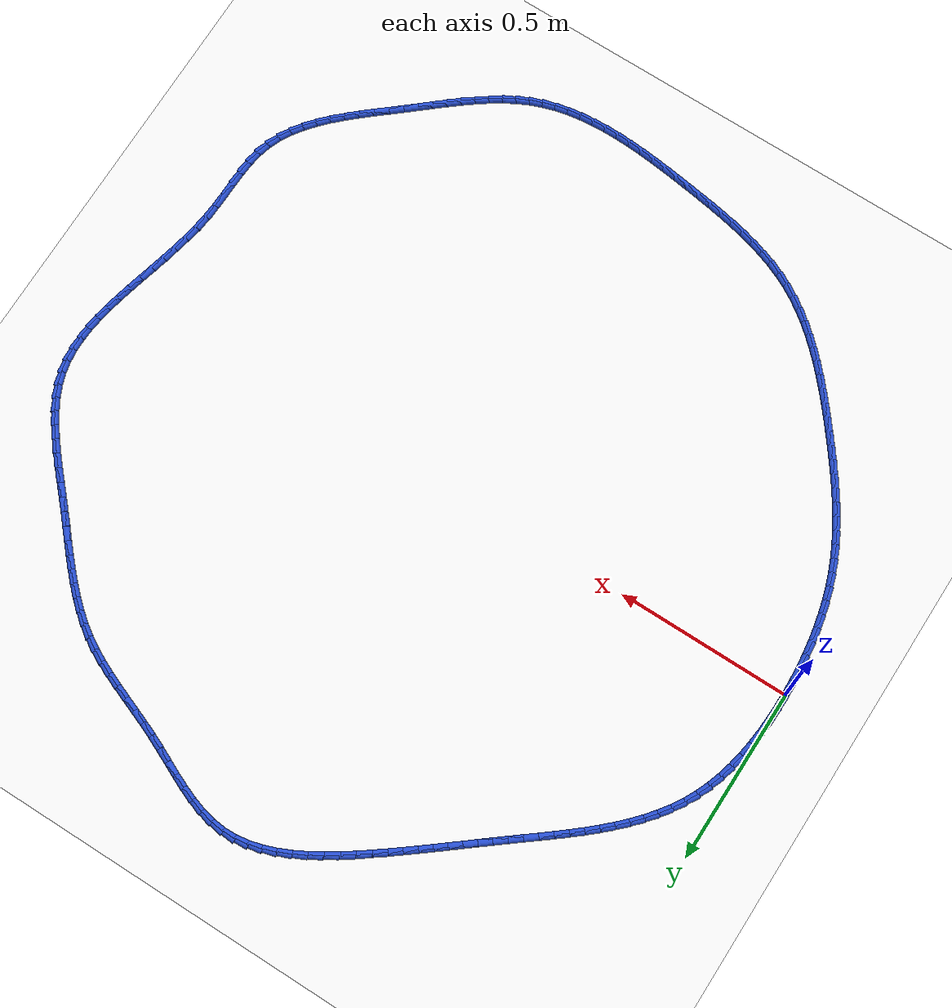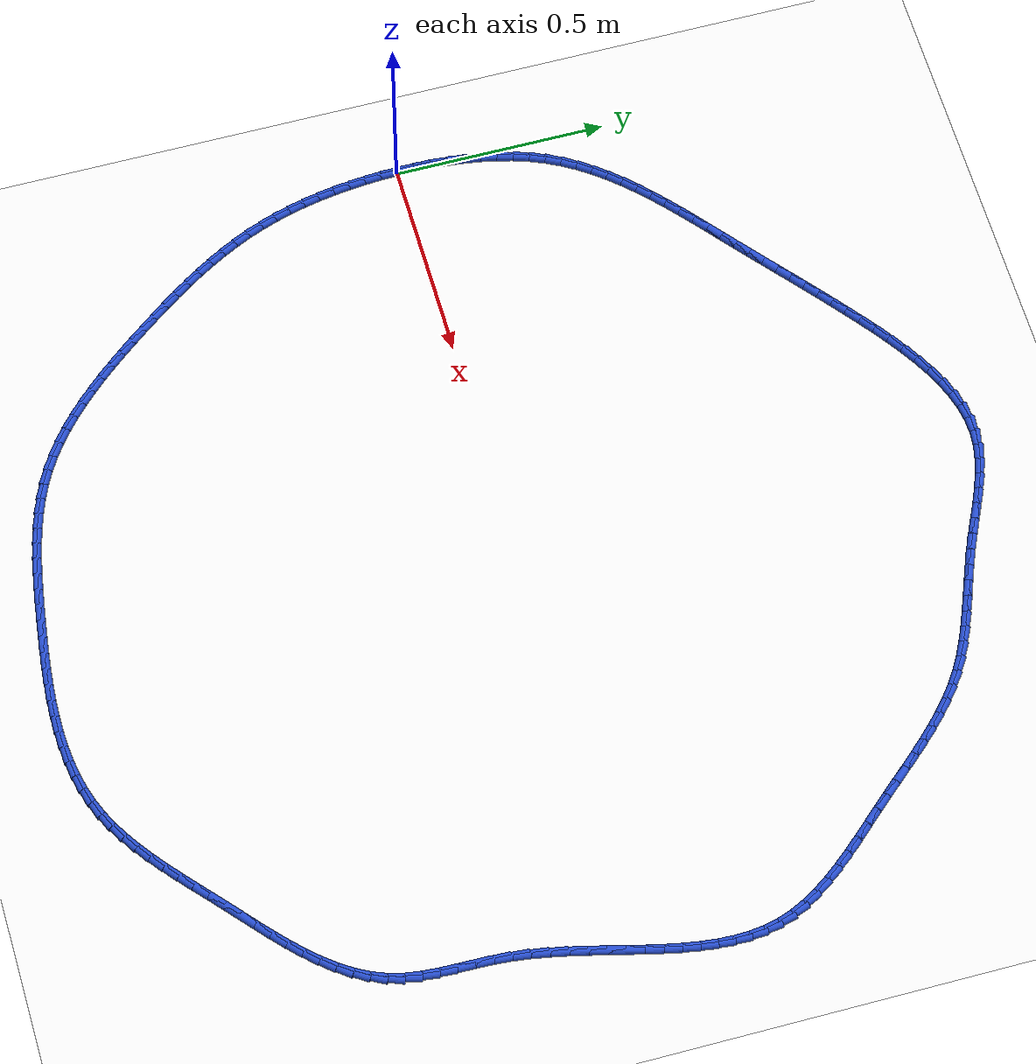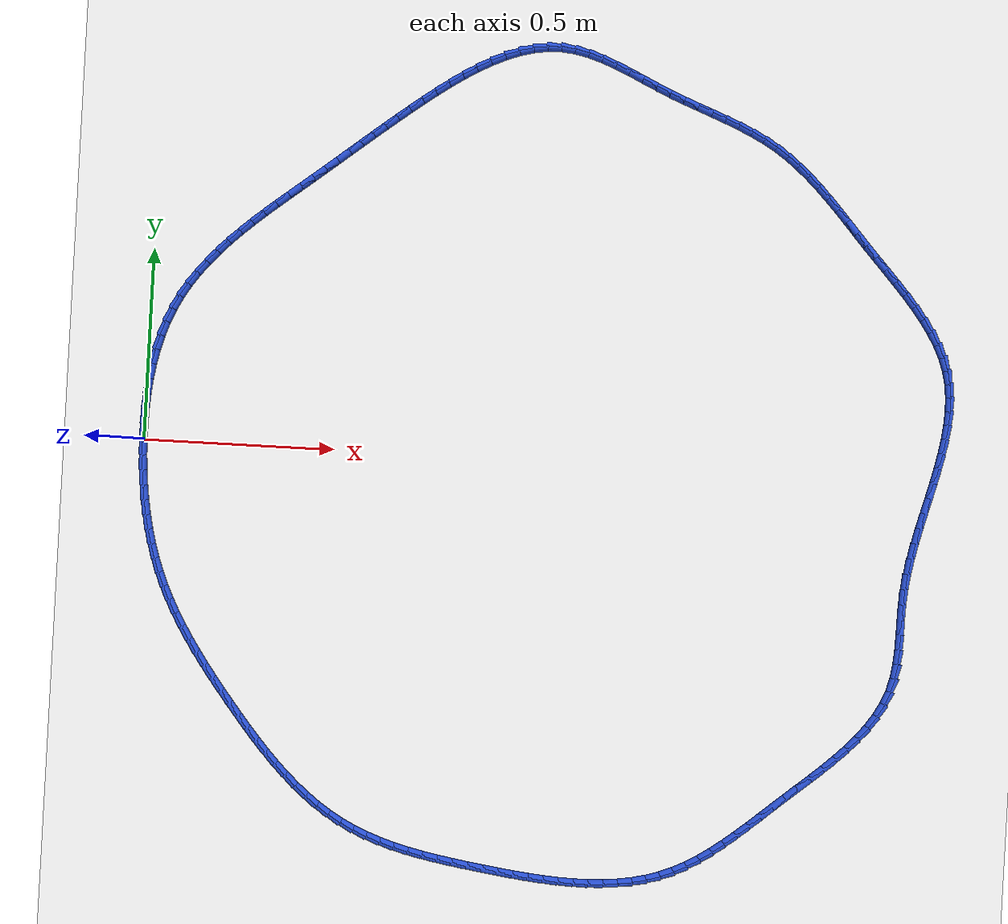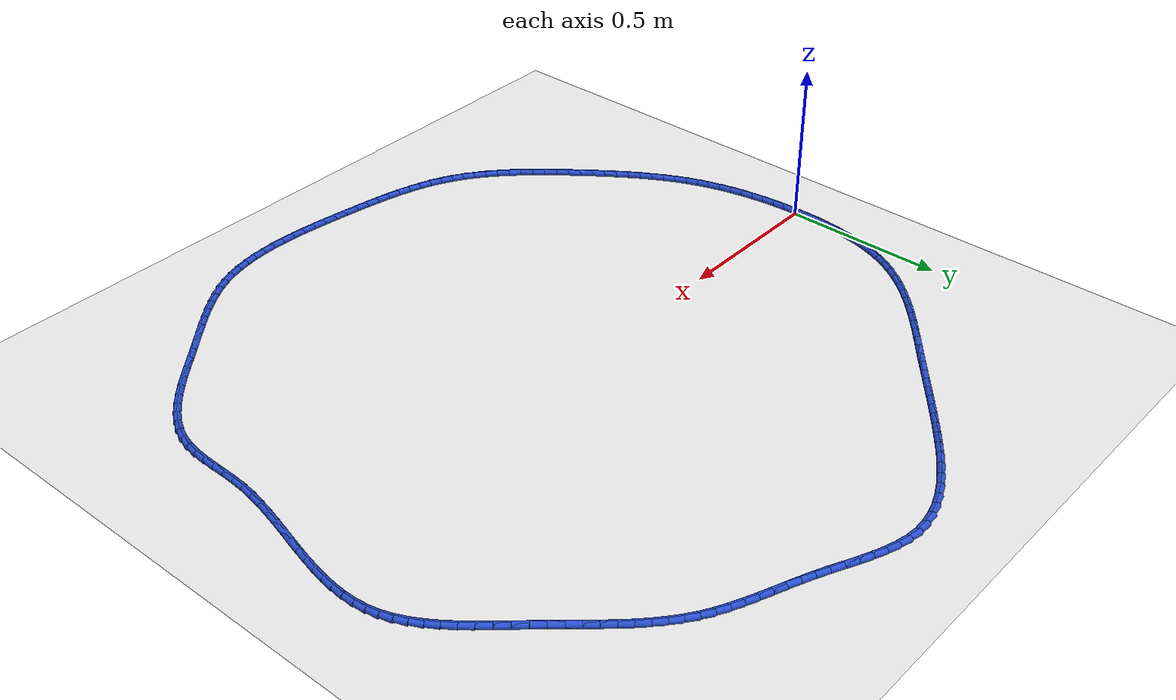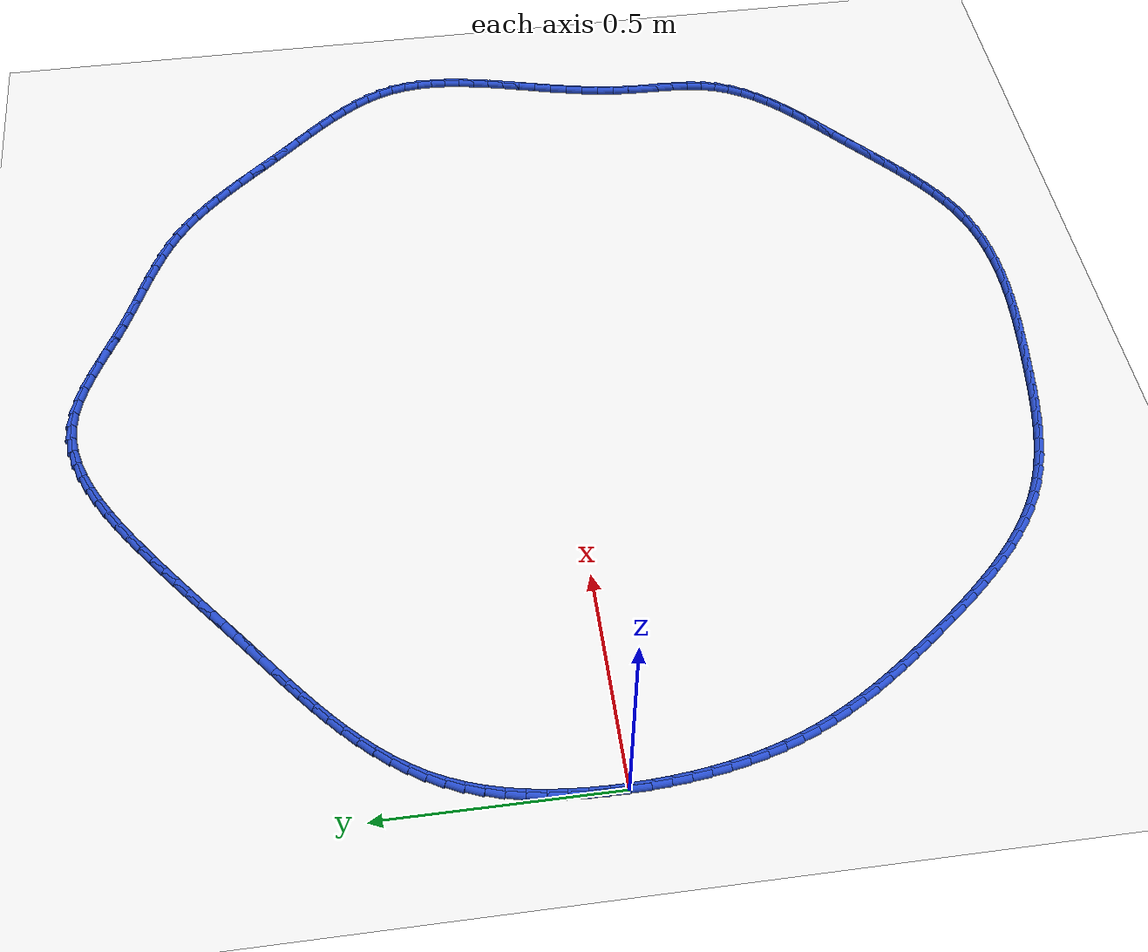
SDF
<sdf version="1.6">
 <world name="default">
  <light name="sun" type="directional">
   <pose>0 0 10 0 -0 0</pose>
   <diffuse>0.8 0.8 0.8 1</diffuse>
   <specular>0.2 0.2 0.2 1</specular>
   <attenuation>
    <range>1000</range>
    <constant>0.9</constant>
    <linear>0.01</linear>
    <quadratic>0.001</quadratic>
   </attenuation>
   <direction>-0.5 0.1 -0.9</direction>
  </light>
  <model name="ground_plane">
   <static>1</static>
   <link name="link">
    <collision name="collision">
     <geometry><plane><normal>0 0 1</normal><size>100 100</size></plane></geometry>
     <surface><friction><ode><mu>100</mu><mu2>50</mu2></ode></friction></surface>
    </collision>
    <visual name="visual">
     <cast_shadows>0</cast_shadows>
     <geometry><plane><normal>0 0 1</normal><size>100 100</size></plane></geometry>
     <material>
      <script><uri>file://media/materials/scripts/gazebo.material</uri><name>Gazebo/WhiteGlow</name></script>
     </material>
    </visual>
   </link>
  </model>
  <gravity>0 0 -9.8</gravity>
  <magnetic_field>6e-06 2.3e-05 -4.2e-05</magnetic_field>
  <atmosphere type="adiabatic"/>
  <physics name="default_physics" default="0" type="ode">
   <max_step_size>0.001</max_step_size>
   <real_time_factor>1</real_time_factor>
   <real_time_update_rate>1000</real_time_update_rate>
  </physics>
  <scene><ambient>0.4 0.4 0.4 1</ambient><background>0.7 0.7 0.7 1</background><shadows>1</shadows></scene>
  <spherical_coordinates>
   <surface_model>EARTH_WGS84</surface_model>
   <latitude_deg>0</latitude_deg>
   <longitude_deg>0</longitude_deg>
   <elevation>0</elevation>
   <heading_deg>0</heading_deg>
  </spherical_coordinates>
  <model name="line">
   <link name="link_0">
    <pose>6.938893903907228e-18 -4.163336342344337e-17 0.01 0 1.57 -1.5676916101894538</pose>
    <collision name="collision">
     <geometry><cylinder><radius>0.01</radius><length>0.08</length></cylinder></geometry>
    </collision>
    <visual name="visual">
     <material>
      <script><name>Gazebo/Blue</name><uri>file://media/materials/scripts/gazebo.material</uri></script>
     </material>
     <geometry><cylinder><radius>0.01</radius><length>0.08</length></cylinder></geometry>
    </visual>
   </link>
   <link name="link_1">
    <pose>-0.0001240107535705233 0.03994256831536844 0.01 0 1.57 1.5407684090416927</pose>
    <collision name="collision">
     <geometry><cylinder><radius>0.01</radius><length>0.08</length></cylinder></geometry>
    </collision>
    <visual name="visual">
     <material>
      <script><name>Gazebo/Blue</name><uri>file://media/materials/scripts/gazebo.material</uri></script>
     </material>
     <geometry><cylinder><radius>0.01</radius><length>0.08</length></cylinder></geometry>
    </visual>
   </link>
   <link name="link_2">
    <pose>0.0010758056912176992 0.07988725638194097 0.01 0 1.57 1.5035129609177584</pose>
    <collision name="collision">
     <geometry><cylinder><radius>0.01</radius><length>0.08</length></cylinder></geometry>
    </collision>
    <visual name="visual">
     <material>
      <script><name>Gazebo/Blue</name><uri>file://media/materials/scripts/gazebo.material</uri></script>
     </material>
     <geometry><cylinder><radius>0.01</radius><length>0.08</length></cylinder></geometry>
    </visual>
   </link>
   <link name="link_3">
    <pose>0.0037561358894148238 0.11966357074974701 0.01 0 1.57 1.461752647181606</pose>
    <collision name="collision">
     <geometry><cylinder><radius>0.01</radius><length>0.08</length></cylinder></geometry>
    </collision>
    <visual name="visual">
     <material>
      <script><name>Gazebo/Blue</name><uri>file://media/materials/scripts/gazebo.material</uri></script>
     </material>
     <geometry><cylinder><radius>0.01</radius><length>0.08</length></cylinder></geometry>
    </visual>
   </link>
   <link name="link_4">
    <pose>0.008073666396071 0.15910101796881604 0.01 0 1.57 1.415074869230866</pose>
    <collision name="collision">
     <geometry><cylinder><radius>0.01</radius><length>0.08</length></cylinder></geometry>
    </collision>
    <visual name="visual">
     <material>
      <script><name>Gazebo/Blue</name><uri>file://media/materials/scripts/gazebo.material</uri></script>
     </material>
     <geometry><cylinder><radius>0.01</radius><length>0.08</length></cylinder></geometry>
    </visual>
   </link>
   <link name="link_5">
    <pose>0.014185083766236384 0.1980291045891775 0.01 0 1.57 1.3630564859032588</pose>
    <collision name="collision">
     <geometry><cylinder><radius>0.01</radius><length>0.08</length></cylinder></geometry>
    </collision>
    <visual name="visual">
     <material>
      <script><name>Gazebo/Blue</name><uri>file://media/materials/scripts/gazebo.material</uri></script>
     </material>
     <geometry><cylinder><radius>0.01</radius><length>0.08</length></cylinder></geometry>
    </visual>
   </link>
   <link name="link_6">
    <pose>0.022247074554961117 0.23627733716086088 0.01 0 1.57 1.3052953716062183</pose>
    <collision name="collision">
     <geometry><cylinder><radius>0.01</radius><length>0.08</length></cylinder></geometry>
    </collision>
    <visual name="visual">
     <material>
      <script><name>Gazebo/Blue</name><uri>file://media/materials/scripts/gazebo.material</uri></script>
     </material>
     <geometry><cylinder><radius>0.01</radius><length>0.08</length></cylinder></geometry>
    </visual>
   </link>
   <link name="link_7">
    <pose>0.03241632531729535 0.2736752222338956 0.01 0 1.57 1.2414569505692037</pose>
    <collision name="collision">
     <geometry><cylinder><radius>0.01</radius><length>0.08</length></cylinder></geometry>
    </collision>
    <visual name="visual">
     <material>
      <script><name>Gazebo/Blue</name><uri>file://media/materials/scripts/gazebo.material</uri></script>
     </material>
     <geometry><cylinder><radius>0.01</radius><length>0.08</length></cylinder></geometry>
    </visual>
   </link>
   <link name="link_8">
    <pose>0.04484952260828924 0.3100522663583111 0.01 0 1.57 1.1713377148081576</pose>
    <collision name="collision">
     <geometry><cylinder><radius>0.01</radius><length>0.08</length></cylinder></geometry>
    </collision>
    <visual name="visual">
     <material>
      <script><name>Gazebo/Blue</name><uri>file://media/materials/scripts/gazebo.material</uri></script>
     </material>
     <geometry><cylinder><radius>0.01</radius><length>0.08</length></cylinder></geometry>
    </visual>
   </link>
   <link name="link_9">
    <pose>0.05970335298299293 0.34523797608413687 0.01 0 1.57 1.095269995409736</pose>
    <collision name="collision">
     <geometry><cylinder><radius>0.01</radius><length>0.08</length></cylinder></geometry>
    </collision>
    <visual name="visual">
     <material>
      <script><name>Gazebo/Blue</name><uri>file://media/materials/scripts/gazebo.material</uri></script>
     </material>
     <geometry><cylinder><radius>0.01</radius><length>0.08</length></cylinder></geometry>
    </visual>
   </link>
   <link name="link_10">
    <pose>0.0771241366133853 0.37906882463720026 0.01 0 1.57 1.0200724143829145</pose>
    <collision name="collision">
     <geometry><cylinder><radius>0.01</radius><length>0.08</length></cylinder></geometry>
    </collision>
    <visual name="visual">
     <material>
      <script><name>Gazebo/Blue</name><uri>file://media/materials/scripts/gazebo.material</uri></script>
     </material>
     <geometry><cylinder><radius>0.01</radius><length>0.08</length></cylinder></geometry>
    </visual>
   </link>
   <link name="link_11">
    <pose>0.09705226196215008 0.41151968061665506 0.01 0 1.57 0.952246324544067</pose>
    <collision name="collision">
     <geometry><cylinder><radius>0.01</radius><length>0.08</length></cylinder></geometry>
    </collision>
    <visual name="visual">
     <material>
      <script><name>Gazebo/Blue</name><uri>file://media/materials/scripts/gazebo.material</uri></script>
     </material>
     <geometry><cylinder><radius>0.01</radius><length>0.08</length></cylinder></geometry>
    </visual>
   </link>
   <link name="link_12">
    <pose>0.11923876802224577 0.44269266398396984 0.01 0 1.57 0.8922600517610706</pose>
    <collision name="collision">
     <geometry><cylinder><radius>0.01</radius><length>0.08</length></cylinder></geometry>
    </collision>
    <visual name="visual">
     <material>
      <script><name>Gazebo/Blue</name><uri>file://media/materials/scripts/gazebo.material</uri></script>
     </material>
     <geometry><cylinder><radius>0.01</radius><length>0.08</length></cylinder></geometry>
    </visual>
   </link>
   <link name="link_13">
    <pose>0.14342765118021208 0.4726946276489668 0.01 0 1.57 0.8400615878281157</pose>
    <collision name="collision">
     <geometry><cylinder><radius>0.01</radius><length>0.08</length></cylinder></geometry>
    </collision>
    <visual name="visual">
     <material>
      <script><name>Gazebo/Blue</name><uri>file://media/materials/scripts/gazebo.material</uri></script>
     </material>
     <geometry><cylinder><radius>0.01</radius><length>0.08</length></cylinder></geometry>
    </visual>
   </link>
   <link name="link_14">
    <pose>0.16936290782258875 0.501632424521469 0.01 0 1.57 0.7954121841297949</pose>
    <collision name="collision">
     <geometry><cylinder><radius>0.01</radius><length>0.08</length></cylinder></geometry>
    </collision>
    <visual name="visual">
     <material>
      <script><name>Gazebo/Blue</name><uri>file://media/materials/scripts/gazebo.material</uri></script>
     </material>
     <geometry><cylinder><radius>0.01</radius><length>0.08</length></cylinder></geometry>
    </visual>
   </link>
   <link name="link_15">
    <pose>0.19678853433591553 0.5296129075112985 0.01 0 1.57 0.757981296980702</pose>
    <collision name="collision">
     <geometry><cylinder><radius>0.01</radius><length>0.08</length></cylinder></geometry>
    </collision>
    <visual name="visual">
     <material>
      <script><name>Gazebo/Blue</name><uri>file://media/materials/scripts/gazebo.material</uri></script>
     </material>
     <geometry><cylinder><radius>0.01</radius><length>0.08</length></cylinder></geometry>
    </visual>
   </link>
   <link name="link_16">
    <pose>0.22544852710673227 0.5567429295282782 0.01 0 1.57 0.727418510321917</pose>
    <collision name="collision">
     <geometry><cylinder><radius>0.01</radius><length>0.08</length></cylinder></geometry>
    </collision>
    <visual name="visual">
     <material>
      <script><name>Gazebo/Blue</name><uri>file://media/materials/scripts/gazebo.material</uri></script>
     </material>
     <geometry><cylinder><radius>0.01</radius><length>0.08</length></cylinder></geometry>
    </visual>
   </link>
   <link name="link_17">
    <pose>0.25508688252157874 0.5831293434822304 0.01 0 1.57 0.7034040983549662</pose>
    <collision name="collision">
     <geometry><cylinder><radius>0.01</radius><length>0.08</length></cylinder></geometry>
    </collision>
    <visual name="visual">
     <material>
      <script><name>Gazebo/Blue</name><uri>file://media/materials/scripts/gazebo.material</uri></script>
     </material>
     <geometry><cylinder><radius>0.01</radius><length>0.08</length></cylinder></geometry>
    </visual>
   </link>
   <link name="link_18">
    <pose>0.28544759696699434 0.6088790022829775 0.01 0 1.57 0.68568303896378</pose>
    <collision name="collision">
     <geometry><cylinder><radius>0.01</radius><length>0.08</length></cylinder></geometry>
    </collision>
    <visual name="visual">
     <material>
      <script><name>Gazebo/Blue</name><uri>file://media/materials/scripts/gazebo.material</uri></script>
     </material>
     <geometry><cylinder><radius>0.01</radius><length>0.08</length></cylinder></geometry>
    </visual>
   </link>
   <link name="link_19">
    <pose>0.31627466682951927 0.6340987588403424 0.01 0 1.57 0.674087767909182</pose>
    <collision name="collision">
     <geometry><cylinder><radius>0.01</radius><length>0.08</length></cylinder></geometry>
    </collision>
    <visual name="visual">
     <material>
      <script><name>Gazebo/Blue</name><uri>file://media/materials/scripts/gazebo.material</uri></script>
     </material>
     <geometry><cylinder><radius>0.01</radius><length>0.08</length></cylinder></geometry>
    </visual>
   </link>
   <link name="link_20">
    <pose>0.34731208849569317 0.6588954660641475 0.01 0 1.57 0.6685542135678278</pose>
    <collision name="collision">
     <geometry><cylinder><radius>0.01</radius><length>0.08</length></cylinder></geometry>
    </collision>
    <visual name="visual">
     <material>
      <script><name>Gazebo/Blue</name><uri>file://media/materials/scripts/gazebo.material</uri></script>
     </material>
     <geometry><cylinder><radius>0.01</radius><length>0.08</length></cylinder></geometry>
    </visual>
   </link>
   <link name="link_21">
    <pose>0.3783038583520557 0.6833759768642154 0.01 0 1.57 0.6691236972101293</pose>
    <collision name="collision">
     <geometry><cylinder><radius>0.01</radius><length>0.08</length></cylinder></geometry>
    </collision>
    <visual name="visual">
     <material>
      <script><name>Gazebo/Blue</name><uri>file://media/materials/scripts/gazebo.material</uri></script>
     </material>
     <geometry><cylinder><radius>0.01</radius><length>0.08</length></cylinder></geometry>
    </visual>
   </link>
   <link name="link_22">
    <pose>0.4089945331427164 0.7076470474561677 0.01 0 1.57 0.673648050897429</pose>
    <collision name="collision">
     <geometry><cylinder><radius>0.01</radius><length>0.08</length></cylinder></geometry>
    </collision>
    <visual name="visual">
     <material>
      <script><name>Gazebo/Blue</name><uri>file://media/materials/scripts/gazebo.material</uri></script>
     </material>
     <geometry><cylinder><radius>0.01</radius><length>0.08</length></cylinder></geometry>
    </visual>
   </link>
   <link name="link_23">
    <pose>0.43924717477919306 0.7317949850369222 0.01 0 1.57 0.677016995341679</pose>
    <collision name="collision">
     <geometry><cylinder><radius>0.01</radius><length>0.08</length></cylinder></geometry>
    </collision>
    <visual name="visual">
     <material>
      <script><name>Gazebo/Blue</name><uri>file://media/materials/scripts/gazebo.material</uri></script>
     </material>
     <geometry><cylinder><radius>0.01</radius><length>0.08</length></cylinder></geometry>
    </visual>
   </link>
   <link name="link_24">
    <pose>0.46918910326626423 0.7558604969463605 0.01 0 1.57 0.6784589051195975</pose>
    <collision name="collision">
     <geometry><cylinder><radius>0.01</radius><length>0.08</length></cylinder></geometry>
    </collision>
    <visual name="visual">
     <material>
      <script><name>Gazebo/Blue</name><uri>file://media/materials/scripts/gazebo.material</uri></script>
     </material>
     <geometry><cylinder><radius>0.01</radius><length>0.08</length></cylinder></geometry>
    </visual>
   </link>
   <link name="link_25">
    <pose>0.49898337237274504 0.7798781243762949 0.01 0 1.57 0.6779350442786455</pose>
    <collision name="collision">
     <geometry><cylinder><radius>0.01</radius><length>0.08</length></cylinder></geometry>
    </collision>
    <visual name="visual">
     <material>
      <script><name>Gazebo/Blue</name><uri>file://media/materials/scripts/gazebo.material</uri></script>
     </material>
     <geometry><cylinder><radius>0.01</radius><length>0.08</length></cylinder></geometry>
    </visual>
   </link>
   <link name="link_26">
    <pose>0.5287930358674504 0.8038824085185382 0.01 0 1.57 0.6754520535355876</pose>
    <collision name="collision">
     <geometry><cylinder><radius>0.01</radius><length>0.08</length></cylinder></geometry>
    </collision>
    <visual name="visual">
     <material>
      <script><name>Gazebo/Blue</name><uri>file://media/materials/scripts/gazebo.material</uri></script>
     </material>
     <geometry><cylinder><radius>0.01</radius><length>0.08</length></cylinder></geometry>
    </visual>
   </link>
   <link name="link_27">
    <pose>0.5587811475191954 0.8279078905649029 0.01 0 1.57 0.6710617325631127</pose>
    <collision name="collision">
     <geometry><cylinder><radius>0.01</radius><length>0.08</length></cylinder></geometry>
    </collision>
    <visual name="visual">
     <material>
      <script><name>Gazebo/Blue</name><uri>file://media/materials/scripts/gazebo.material</uri></script>
     </material>
     <geometry><cylinder><radius>0.01</radius><length>0.08</length></cylinder></geometry>
    </visual>
   </link>
   <link name="link_28">
    <pose>0.5891107610967954 0.8519891117072016 0.01 0 1.57 0.6648584566163249</pose>
    <collision name="collision">
     <geometry><cylinder><radius>0.01</radius><length>0.08</length></cylinder></geometry>
    </collision>
    <visual name="visual">
     <material>
      <script><name>Gazebo/Blue</name><uri>file://media/materials/scripts/gazebo.material</uri></script>
     </material>
     <geometry><cylinder><radius>0.01</radius><length>0.08</length></cylinder></geometry>
    </visual>
   </link>
   <link name="link_29">
    <pose>0.6199449303690652 0.8761606131372471 0.01 0 1.57 0.6569744422796842</pose>
    <collision name="collision">
     <geometry><cylinder><radius>0.01</radius><length>0.08</length></cylinder></geometry>
    </collision>
    <visual name="visual">
     <material>
      <script><name>Gazebo/Blue</name><uri>file://media/materials/scripts/gazebo.material</uri></script>
     </material>
     <geometry><cylinder><radius>0.01</radius><length>0.08</length></cylinder></geometry>
    </visual>
   </link>
   <link name="link_30">
    <pose>0.6514467091048195 0.9004569360468514 0.01 0 1.57 0.6474209578376263</pose>
    <collision name="collision">
     <geometry><cylinder><radius>0.01</radius><length>0.08</length></cylinder></geometry>
    </collision>
    <visual name="visual">
     <material>
      <script><name>Gazebo/Blue</name><uri>file://media/materials/scripts/gazebo.material</uri></script>
     </material>
     <geometry><cylinder><radius>0.01</radius><length>0.08</length></cylinder></geometry>
    </visual>
   </link>
   <link name="link_31">
    <pose>0.6837731962474867 0.9249003783235316 0.01 0 1.57 0.6331195395096945</pose>
    <collision name="collision">
     <geometry><cylinder><radius>0.01</radius><length>0.08</length></cylinder></geometry>
    </collision>
    <visual name="visual">
     <material>
      <script><name>Gazebo/Blue</name><uri>file://media/materials/scripts/gazebo.material</uri></script>
     </material>
     <geometry><cylinder><radius>0.01</radius><length>0.08</length></cylinder></geometry>
    </visual>
   </link>
   <link name="link_32">
    <pose>0.7169545861808617 0.9492523181738578 0.01 0 1.57 0.6109323411636277</pose>
    <collision name="collision">
     <geometry><cylinder><radius>0.01</radius><length>0.08</length></cylinder></geometry>
    </collision>
    <visual name="visual">
     <material>
      <script><name>Gazebo/Blue</name><uri>file://media/materials/scripts/gazebo.material</uri></script>
     </material>
     <geometry><cylinder><radius>0.01</radius><length>0.08</length></cylinder></geometry>
    </visual>
   </link>
   <link name="link_33">
    <pose>0.7508995162889793 0.9730242088711587 0.01 0 1.57 0.580331755530792</pose>
    <collision name="collision">
     <geometry><cylinder><radius>0.01</radius><length>0.08</length></cylinder></geometry>
    </collision>
    <visual name="visual">
     <material>
      <script><name>Gazebo/Blue</name><uri>file://media/materials/scripts/gazebo.material</uri></script>
     </material>
     <geometry><cylinder><radius>0.01</radius><length>0.08</length></cylinder></geometry>
    </visual>
   </link>
   <link name="link_34">
    <pose>0.7855117392639189 0.9957174606117435 0.01 0 1.57 0.5405461772761361</pose>
    <collision name="collision">
     <geometry><cylinder><radius>0.01</radius><length>0.08</length></cylinder></geometry>
    </collision>
    <visual name="visual">
     <material>
      <script><name>Gazebo/Blue</name><uri>file://media/materials/scripts/gazebo.material</uri></script>
     </material>
     <geometry><cylinder><radius>0.01</radius><length>0.08</length></cylinder></geometry>
    </visual>
   </link>
   <link name="link_35">
    <pose>0.820695007797759 1.0168334835919195 0.01 0 1.57 0.4904499565831554</pose>
    <collision name="collision">
     <geometry><cylinder><radius>0.01</radius><length>0.08</length></cylinder></geometry>
    </collision>
    <visual name="visual">
     <material>
      <script><name>Gazebo/Blue</name><uri>file://media/materials/scripts/gazebo.material</uri></script>
     </material>
     <geometry><cylinder><radius>0.01</radius><length>0.08</length></cylinder></geometry>
    </visual>
   </link>
   <link name="link_36">
    <pose>0.8563530745825789 1.0358736880079955 0.01 0 1.57 0.42859240694661394</pose>
    <collision name="collision">
     <geometry><cylinder><radius>0.01</radius><length>0.08</length></cylinder></geometry>
    </collision>
    <visual name="visual">
     <material>
      <script><name>Gazebo/Blue</name><uri>file://media/materials/scripts/gazebo.material</uri></script>
     </material>
     <geometry><cylinder><radius>0.01</radius><length>0.08</length></cylinder></geometry>
    </visual>
   </link>
   <link name="link_37">
    <pose>0.8923896923104576 1.05233948405628 0.01 0 1.57 0.35328473260305254</pose>
    <collision name="collision">
     <geometry><cylinder><radius>0.01</radius><length>0.08</length></cylinder></geometry>
    </collision>
    <visual name="visual">
     <material>
      <script><name>Gazebo/Blue</name><uri>file://media/materials/scripts/gazebo.material</uri></script>
     </material>
     <geometry><cylinder><radius>0.01</radius><length>0.08</length></cylinder></geometry>
    </visual>
   </link>
   <link name="link_38">
    <pose>0.9287086136734736 1.0657322819330808 0.01 0 1.57 0.2628145662707853</pose>
    <collision name="collision">
     <geometry><cylinder><radius>0.01</radius><length>0.08</length></cylinder></geometry>
    </collision>
    <visual name="visual">
     <material>
      <script><name>Gazebo/Blue</name><uri>file://media/materials/scripts/gazebo.material</uri></script>
     </material>
     <geometry><cylinder><radius>0.01</radius><length>0.08</length></cylinder></geometry>
    </visual>
   </link>
   <link name="link_39">
    <pose>0.9652135913637067 1.0755534918347063 0.01 0 1.57 0.15587947604825492</pose>
    <collision name="collision">
     <geometry><cylinder><radius>0.01</radius><length>0.08</length></cylinder></geometry>
    </collision>
    <visual name="visual">
     <material>
      <script><name>Gazebo/Blue</name><uri>file://media/materials/scripts/gazebo.material</uri></script>
     </material>
     <geometry><cylinder><radius>0.01</radius><length>0.08</length></cylinder></geometry>
    </visual>
   </link>
   <link name="link_40">
    <pose>1.0018083780732354 1.0813045239574648 0.01 0 1.57 0.032301357666598744</pose>
    <collision name="collision">
     <geometry><cylinder><radius>0.01</radius><length>0.08</length></cylinder></geometry>
    </collision>
    <visual name="visual">
     <material>
      <script><name>Gazebo/Blue</name><uri>file://media/materials/scripts/gazebo.material</uri></script>
     </material>
     <geometry><cylinder><radius>0.01</radius><length>0.08</length></cylinder></geometry>
    </visual>
   </link>
   <link name="link_41">
    <pose>1.0383967264941383 1.0824867884976643 0.01 0 1.57 -0.10108205714212606</pose>
    <collision name="collision">
     <geometry><cylinder><radius>0.01</radius><length>0.08</length></cylinder></geometry>
    </collision>
    <visual name="visual">
     <material>
      <script><name>Gazebo/Blue</name><uri>file://media/materials/scripts/gazebo.material</uri></script>
     </material>
     <geometry><cylinder><radius>0.01</radius><length>0.08</length></cylinder></geometry>
    </visual>
   </link>
   <link name="link_42">
    <pose>1.0749014130056576 1.078784200592612 0.01 0 1.57 -0.2168176558800977</pose>
    <collision name="collision">
     <geometry><cylinder><radius>0.01</radius><length>0.08</length></cylinder></geometry>
    </collision>
    <visual name="visual">
     <material>
      <script><name>Gazebo/Blue</name><uri>file://media/materials/scripts/gazebo.material</uri></script>
     </material>
     <geometry><cylinder><radius>0.01</radius><length>0.08</length></cylinder></geometry>
    </visual>
   </link>
   <link name="link_43">
    <pose>1.11133668697493 1.070758227250425 0.01 0 1.57 -0.3065613332785043</pose>
    <collision name="collision">
     <geometry><cylinder><radius>0.01</radius><length>0.08</length></cylinder></geometry>
    </collision>
    <visual name="visual">
     <material>
      <script><name>Gazebo/Blue</name><uri>file://media/materials/scripts/gazebo.material</uri></script>
     </material>
     <geometry><cylinder><radius>0.01</radius><length>0.08</length></cylinder></geometry>
    </visual>
   </link>
   <link name="link_44">
    <pose>1.1477442572084502 1.0592337693402194 0.01 0 1.57 -0.37170293703911716</pose>
    <collision name="collision">
     <geometry><cylinder><radius>0.01</radius><length>0.08</length></cylinder></geometry>
    </collision>
    <visual name="visual">
     <material>
      <script><name>Gazebo/Blue</name><uri>file://media/materials/scripts/gazebo.material</uri></script>
     </material>
     <geometry><cylinder><radius>0.01</radius><length>0.08</length></cylinder></geometry>
    </visual>
   </link>
   <link name="link_45">
    <pose>1.1841658377890667 1.045035778350141 0.01 0 1.57 -0.41442782550386414</pose>
    <collision name="collision">
     <geometry><cylinder><radius>0.01</radius><length>0.08</length></cylinder></geometry>
    </collision>
    <visual name="visual">
     <material>
      <script><name>Gazebo/Blue</name><uri>file://media/materials/scripts/gazebo.material</uri></script>
     </material>
     <geometry><cylinder><radius>0.01</radius><length>0.08</length></cylinder></geometry>
    </visual>
   </link>
   <link name="link_46">
    <pose>1.2206431427996258 1.028989205768336 0.01 0 1.57 -0.43667181638576197</pose>
    <collision name="collision">
     <geometry><cylinder><radius>0.01</radius><length>0.08</length></cylinder></geometry>
    </collision>
    <visual name="visual">
     <material>
      <script><name>Gazebo/Blue</name><uri>file://media/materials/scripts/gazebo.material</uri></script>
     </material>
     <geometry><cylinder><radius>0.01</radius><length>0.08</length></cylinder></geometry>
    </visual>
   </link>
   <link name="link_47">
    <pose>1.2572178863229766 1.0119190030829506 0.01 0 1.57 -0.43965867992340646</pose>
    <collision name="collision">
     <geometry><cylinder><radius>0.01</radius><length>0.08</length></cylinder></geometry>
    </collision>
    <visual name="visual">
     <material>
      <script><name>Gazebo/Blue</name><uri>file://media/materials/scripts/gazebo.material</uri></script>
     </material>
     <geometry><cylinder><radius>0.01</radius><length>0.08</length></cylinder></geometry>
    </visual>
   </link>
   <link name="link_48">
    <pose>1.2939317824419656 0.9946501217821306 0.01 0 1.57 -0.42378051686365903</pose>
    <collision name="collision">
     <geometry><cylinder><radius>0.01</radius><length>0.08</length></cylinder></geometry>
    </collision>
    <visual name="visual">
     <material>
      <script><name>Gazebo/Blue</name><uri>file://media/materials/scripts/gazebo.material</uri></script>
     </material>
     <geometry><cylinder><radius>0.01</radius><length>0.08</length></cylinder></geometry>
    </visual>
   </link>
   <link name="link_49">
    <pose>1.3308263294866667 0.9780064496123787 0.01 0 1.57 -0.3968934051463443</pose>
    <collision name="collision">
     <geometry><cylinder><radius>0.01</radius><length>0.08</length></cylinder></geometry>
    </collision>
    <visual name="visual">
     <material>
      <script><name>Gazebo/Blue</name><uri>file://media/materials/scripts/gazebo.material</uri></script>
     </material>
     <geometry><cylinder><radius>0.01</radius><length>0.08</length></cylinder></geometry>
    </visual>
   </link>
   <link name="link_50">
    <pose>1.3678752864865296 0.9624778943046117 0.01 0 1.57 -0.378765844302604</pose>
    <collision name="collision">
     <geometry><cylinder><radius>0.01</radius><length>0.08</length></cylinder></geometry>
    </collision>
    <visual name="visual">
     <material>
      <script><name>Gazebo/Blue</name><uri>file://media/materials/scripts/gazebo.material</uri></script>
     </material>
     <geometry><cylinder><radius>0.01</radius><length>0.08</length></cylinder></geometry>
    </visual>
   </link>
   <link name="link_51">
    <pose>1.4048887014416773 0.9477472071588104 0.01 0 1.57 -0.37260547723734655</pose>
    <collision name="collision">
     <geometry><cylinder><radius>0.01</radius><length>0.08</length></cylinder></geometry>
    </collision>
    <visual name="visual">
     <material>
      <script><name>Gazebo/Blue</name><uri>file://media/materials/scripts/gazebo.material</uri></script>
     </material>
     <geometry><cylinder><radius>0.01</radius><length>0.08</length></cylinder></geometry>
    </visual>
   </link>
   <link name="link_52">
    <pose>1.4416523811825135 0.9333776214674365 0.01 0 1.57 -0.3787322960485489</pose>
    <collision name="collision">
     <geometry><cylinder><radius>0.01</radius><length>0.08</length></cylinder></geometry>
    </collision>
    <visual name="visual">
     <material>
      <script><name>Gazebo/Blue</name><uri>file://media/materials/scripts/gazebo.material</uri></script>
     </material>
     <geometry><cylinder><radius>0.01</radius><length>0.08</length></cylinder></geometry>
    </visual>
   </link>
   <link name="link_53">
    <pose>1.4779521325394394 0.9189323705229513 0.01 0 1.57 -0.39754681492962307</pose>
    <collision name="collision">
     <geometry><cylinder><radius>0.01</radius><length>0.08</length></cylinder></geometry>
    </collision>
    <visual name="visual">
     <material>
      <script><name>Gazebo/Blue</name><uri>file://media/materials/scripts/gazebo.material</uri></script>
     </material>
     <geometry><cylinder><radius>0.01</radius><length>0.08</length></cylinder></geometry>
    </visual>
   </link>
   <link name="link_54">
    <pose>1.5135737623428582 0.9039746876178164 0.01 0 1.57 -0.4295071344164393</pose>
    <collision name="collision">
     <geometry><cylinder><radius>0.01</radius><length>0.08</length></cylinder></geometry>
    </collision>
    <visual name="visual">
     <material>
      <script><name>Gazebo/Blue</name><uri>file://media/materials/scripts/gazebo.material</uri></script>
     </material>
     <geometry><cylinder><radius>0.01</radius><length>0.08</length></cylinder></geometry>
    </visual>
   </link>
   <link name="link_55">
    <pose>1.5483030774231727 0.8880678060444939 0.01 0 1.57 -0.4750370412200318</pose>
    <collision name="collision">
     <geometry><cylinder><radius>0.01</radius><length>0.08</length></cylinder></geometry>
    </collision>
    <visual name="visual">
     <material>
      <script><name>Gazebo/Blue</name><uri>file://media/materials/scripts/gazebo.material</uri></script>
     </material>
     <geometry><cylinder><radius>0.01</radius><length>0.08</length></cylinder></geometry>
    </visual>
   </link>
   <link name="link_56">
    <pose>1.5819258846107855 0.8707749590954453 0.01 0 1.57 -0.5343497594100991</pose>
    <collision name="collision">
     <geometry><cylinder><radius>0.01</radius><length>0.08</length></cylinder></geometry>
    </collision>
    <visual name="visual">
     <material>
      <script><name>Gazebo/Blue</name><uri>file://media/materials/scripts/gazebo.material</uri></script>
     </material>
     <geometry><cylinder><radius>0.01</radius><length>0.08</length></cylinder></geometry>
    </visual>
   </link>
   <link name="link_57">
    <pose>1.6142279907360977 0.8516593800631319 0.01 0 1.57 -0.6037393953036544</pose>
    <collision name="collision">
     <geometry><cylinder><radius>0.01</radius><length>0.08</length></cylinder></geometry>
    </collision>
    <visual name="visual">
     <material>
      <script><name>Gazebo/Blue</name><uri>file://media/materials/scripts/gazebo.material</uri></script>
     </material>
     <geometry><cylinder><radius>0.01</radius><length>0.08</length></cylinder></geometry>
    </visual>
   </link>
   <link name="link_58">
    <pose>1.645065242448299 0.8303927621386604 0.01 0 1.57 -0.6678727166397935</pose>
    <collision name="collision">
     <geometry><cylinder><radius>0.01</radius><length>0.08</length></cylinder></geometry>
    </collision>
    <visual name="visual">
     <material>
      <script><name>Gazebo/Blue</name><uri>file://media/materials/scripts/gazebo.material</uri></script>
     </material>
     <geometry><cylinder><radius>0.01</radius><length>0.08</length></cylinder></geometry>
    </visual>
   </link>
   <link name="link_59">
    <pose>1.6745890348172443 0.8071044689112994 0.01 0 1.57 -0.7223083172210687</pose>
    <collision name="collision">
     <geometry><cylinder><radius>0.01</radius><length>0.08</length></cylinder></geometry>
    </collision>
    <visual name="visual">
     <material>
      <script><name>Gazebo/Blue</name><uri>file://media/materials/scripts/gazebo.material</uri></script>
     </material>
     <geometry><cylinder><radius>0.01</radius><length>0.08</length></cylinder></geometry>
    </visual>
   </link>
   <link name="link_60">
    <pose>1.7030287063058787 0.7820445629192994 0.01 0 1.57 -0.7668752382026103</pose>
    <collision name="collision">
     <geometry><cylinder><radius>0.01</radius><length>0.08</length></cylinder></geometry>
    </collision>
    <visual name="visual">
     <material>
      <script><name>Gazebo/Blue</name><uri>file://media/materials/scripts/gazebo.material</uri></script>
     </material>
     <geometry><cylinder><radius>0.01</radius><length>0.08</length></cylinder></geometry>
    </visual>
   </link>
   <link name="link_61">
    <pose>1.730613595795561 0.7554631073488457 0.01 0 1.57 -0.8016976987750488</pose>
    <collision name="collision">
     <geometry><cylinder><radius>0.01</radius><length>0.08</length></cylinder></geometry>
    </collision>
    <visual name="visual">
     <material>
      <script><name>Gazebo/Blue</name><uri>file://media/materials/scripts/gazebo.material</uri></script>
     </material>
     <geometry><cylinder><radius>0.01</radius><length>0.08</length></cylinder></geometry>
    </visual>
   </link>
   <link name="link_62">
    <pose>1.7575730421676499 0.7276101653861247 0.01 0 1.57 -0.8270608844257014</pose>
    <collision name="collision">
     <geometry><cylinder><radius>0.01</radius><length>0.08</length></cylinder></geometry>
    </collision>
    <visual name="visual">
     <material>
      <script><name>Gazebo/Blue</name><uri>file://media/materials/scripts/gazebo.material</uri></script>
     </material>
     <geometry><cylinder><radius>0.01</radius><length>0.08</length></cylinder></geometry>
    </visual>
   </link>
   <link name="link_63">
    <pose>1.7841363843035047 0.6987358002173216 0.01 0 1.57 -0.8433100471853017</pose>
    <collision name="collision">
     <geometry><cylinder><radius>0.01</radius><length>0.08</length></cylinder></geometry>
    </collision>
    <visual name="visual">
     <material>
      <script><name>Gazebo/Blue</name><uri>file://media/materials/scripts/gazebo.material</uri></script>
     </material>
     <geometry><cylinder><radius>0.01</radius><length>0.08</length></cylinder></geometry>
    </visual>
   </link>
   <link name="link_64">
    <pose>1.8105329610844838 0.6690900750286224 0.01 0 1.57 -0.8507846420287272</pose>
    <collision name="collision">
     <geometry><cylinder><radius>0.01</radius><length>0.08</length></cylinder></geometry>
    </collision>
    <visual name="visual">
     <material>
      <script><name>Gazebo/Blue</name><uri>file://media/materials/scripts/gazebo.material</uri></script>
     </material>
     <geometry><cylinder><radius>0.01</radius><length>0.08</length></cylinder></geometry>
    </visual>
   </link>
   <link name="link_65">
    <pose>1.8369921113919465 0.638923053006213 0.01 0 1.57 -0.8497825057222906</pose>
    <collision name="collision">
     <geometry><cylinder><radius>0.01</radius><length>0.08</length></cylinder></geometry>
    </collision>
    <visual name="visual">
     <material>
      <script><name>Gazebo/Blue</name><uri>file://media/materials/scripts/gazebo.material</uri></script>
     </material>
     <geometry><cylinder><radius>0.01</radius><length>0.08</length></cylinder></geometry>
    </visual>
   </link>
   <link name="link_66">
    <pose>1.863743174107252 0.6084847973362784 0.01 0 1.57 -0.8410196187090825</pose>
    <collision name="collision">
     <geometry><cylinder><radius>0.01</radius><length>0.08</length></cylinder></geometry>
    </collision>
    <visual name="visual">
     <material>
      <script><name>Gazebo/Blue</name><uri>file://media/materials/scripts/gazebo.material</uri></script>
     </material>
     <geometry><cylinder><radius>0.01</radius><length>0.08</length></cylinder></geometry>
    </visual>
   </link>
   <link name="link_67">
    <pose>1.8909973083321887 0.5780167567222744 0.01 0 1.57 -0.8341662579337321</pose>
    <collision name="collision">
     <geometry><cylinder><radius>0.01</radius><length>0.08</length></cylinder></geometry>
    </collision>
    <visual name="visual">
     <material>
      <script><name>Gazebo/Blue</name><uri>file://media/materials/scripts/gazebo.material</uri></script>
     </material>
     <geometry><cylinder><radius>0.01</radius><length>0.08</length></cylinder></geometry>
    </visual>
   </link>
   <link name="link_68">
    <pose>1.918596390025168 0.5475853951683565 0.01 0 1.57 -0.8379853898247611</pose>
    <collision name="collision">
     <geometry><cylinder><radius>0.01</radius><length>0.08</length></cylinder></geometry>
    </collision>
    <visual name="visual">
     <material>
      <script><name>Gazebo/Blue</name><uri>file://media/materials/scripts/gazebo.material</uri></script>
     </material>
     <geometry><cylinder><radius>0.01</radius><length>0.08</length></cylinder></geometry>
    </visual>
   </link>
   <link name="link_69">
    <pose>1.9460382709802724 0.5170941609385215 0.01 0 1.57 -0.8529414000449392</pose>
    <collision name="collision">
     <geometry><cylinder><radius>0.01</radius><length>0.08</length></cylinder></geometry>
    </collision>
    <visual name="visual">
     <material>
      <script><name>Gazebo/Blue</name><uri>file://media/materials/scripts/gazebo.material</uri></script>
     </material>
     <geometry><cylinder><radius>0.01</radius><length>0.08</length></cylinder></geometry>
    </visual>
   </link>
   <link name="link_70">
    <pose>1.9728076829589825 0.4864402853735151 0.01 0 1.57 -0.8795880110072843</pose>
    <collision name="collision">
     <geometry><cylinder><radius>0.01</radius><length>0.08</length></cylinder></geometry>
    </collision>
    <visual name="visual">
     <material>
      <script><name>Gazebo/Blue</name><uri>file://media/materials/scripts/gazebo.material</uri></script>
     </material>
     <geometry><cylinder><radius>0.01</radius><length>0.08</length></cylinder></geometry>
    </visual>
   </link>
   <link name="link_71">
    <pose>1.9983893577227787 0.45552099981408367 0.01 0 1.57 -0.9188990571414987</pose>
    <collision name="collision">
     <geometry><cylinder><radius>0.01</radius><length>0.08</length></cylinder></geometry>
    </collision>
    <visual name="visual">
     <material>
      <script><name>Gazebo/Blue</name><uri>file://media/materials/scripts/gazebo.material</uri></script>
     </material>
     <geometry><cylinder><radius>0.01</radius><length>0.08</length></cylinder></geometry>
    </visual>
   </link>
   <link name="link_72">
    <pose>2.022268027033141 0.42423353560097415 0.01 0 1.57 -0.9722284180211227</pose>
    <collision name="collision">
     <geometry><cylinder><radius>0.01</radius><length>0.08</length></cylinder></geometry>
    </collision>
    <visual name="visual">
     <material>
      <script><name>Gazebo/Blue</name><uri>file://media/materials/scripts/gazebo.material</uri></script>
     </material>
     <geometry><cylinder><radius>0.01</radius><length>0.08</length></cylinder></geometry>
    </visual>
   </link>
   <link name="link_73">
    <pose>2.0439284226515504 0.39247512407493274 0.01 0 1.57 -1.04118990578017</pose>
    <collision name="collision">
     <geometry><cylinder><radius>0.01</radius><length>0.08</length></cylinder></geometry>
    </collision>
    <visual name="visual">
     <material>
      <script><name>Gazebo/Blue</name><uri>file://media/materials/scripts/gazebo.material</uri></script>
     </material>
     <geometry><cylinder><radius>0.01</radius><length>0.08</length></cylinder></geometry>
    </visual>
   </link>
   <link name="link_74">
    <pose>2.0628552763394854 0.3601429965767052 0.01 0 1.57 -1.1273738765443044</pose>
    <collision name="collision">
     <geometry><cylinder><radius>0.01</radius><length>0.08</length></cylinder></geometry>
    </collision>
    <visual name="visual">
     <material>
      <script><name>Gazebo/Blue</name><uri>file://media/materials/scripts/gazebo.material</uri></script>
     </material>
     <geometry><cylinder><radius>0.01</radius><length>0.08</length></cylinder></geometry>
    </visual>
   </link>
   <link name="link_75">
    <pose>2.078533319858429 0.32713438444703874 0.01 0 1.57 -1.2317824669100814</pose>
    <collision name="collision">
     <geometry><cylinder><radius>0.01</radius><length>0.08</length></cylinder></geometry>
    </collision>
    <visual name="visual">
     <material>
      <script><name>Gazebo/Blue</name><uri>file://media/materials/scripts/gazebo.material</uri></script>
     </material>
     <geometry><cylinder><radius>0.01</radius><length>0.08</length></cylinder></geometry>
    </visual>
   </link>
   <link name="link_76">
    <pose>2.090447825521905 0.29334661143787305 0.01 0 1.57 -1.3472417434244817</pose>
    <collision name="collision">
     <geometry><cylinder><radius>0.01</radius><length>0.08</length></cylinder></geometry>
    </collision>
    <visual name="visual">
     <material>
      <script><name>Gazebo/Blue</name><uri>file://media/materials/scripts/gazebo.material</uri></script>
     </material>
     <geometry><cylinder><radius>0.01</radius><length>0.08</length></cylinder></geometry>
    </visual>
   </link>
   <link name="link_77">
    <pose>2.098320919666069 0.2587174931707878 0.01 0 1.57 -1.4538908434314441</pose>
    <collision name="collision">
     <geometry><cylinder><radius>0.01</radius><length>0.08</length></cylinder></geometry>
    </collision>
    <visual name="visual">
     <material>
      <script><name>Gazebo/Blue</name><uri>file://media/materials/scripts/gazebo.material</uri></script>
     </material>
     <geometry><cylinder><radius>0.01</radius><length>0.08</length></cylinder></geometry>
    </visual>
   </link>
   <link name="link_78">
    <pose>2.1024817221541676 0.22328861510204226 0.01 0 1.57 -1.54665165139785</pose>
    <collision name="collision">
     <geometry><cylinder><radius>0.01</radius><length>0.08</length></cylinder></geometry>
    </collision>
    <visual name="visual">
     <material>
      <script><name>Gazebo/Blue</name><uri>file://media/materials/scripts/gazebo.material</uri></script>
     </material>
     <geometry><cylinder><radius>0.01</radius><length>0.08</length></cylinder></geometry>
    </visual>
   </link>
   <link name="link_79">
    <pose>2.103355220820193 0.1871179519952454 0.01 0 1.57 1.5168845503592499</pose>
    <collision name="collision">
     <geometry><cylinder><radius>0.01</radius><length>0.08</length></cylinder></geometry>
    </collision>
    <visual name="visual">
     <material>
      <script><name>Gazebo/Blue</name><uri>file://media/materials/scripts/gazebo.material</uri></script>
     </material>
     <geometry><cylinder><radius>0.01</radius><length>0.08</length></cylinder></geometry>
    </visual>
   </link>
   <link name="link_80">
    <pose>2.101366403498139 0.15026347861400718 0.01 0 1.57 1.4532481896830016</pose>
    <collision name="collision">
     <geometry><cylinder><radius>0.01</radius><length>0.08</length></cylinder></geometry>
    </collision>
    <visual name="visual">
     <material>
      <script><name>Gazebo/Blue</name><uri>file://media/materials/scripts/gazebo.material</uri></script>
     </material>
     <geometry><cylinder><radius>0.01</radius><length>0.08</length></cylinder></geometry>
    </visual>
   </link>
   <link name="link_81">
    <pose>2.0969402580219993 0.11278316972193697 0.01 0 1.57 1.4031650091620156</pose>
    <collision name="collision">
     <geometry><cylinder><radius>0.01</radius><length>0.08</length></cylinder></geometry>
    </collision>
    <visual name="visual">
     <material>
      <script><name>Gazebo/Blue</name><uri>file://media/materials/scripts/gazebo.material</uri></script>
     </material>
     <geometry><cylinder><radius>0.01</radius><length>0.08</length></cylinder></geometry>
    </visual>
   </link>
   <link name="link_82">
    <pose>2.0905017722257675 0.0747350000826439 0.01 0 1.57 1.3655771730965014</pose>
    <collision name="collision">
     <geometry><cylinder><radius>0.01</radius><length>0.08</length></cylinder></geometry>
    </collision>
    <visual name="visual">
     <material>
      <script><name>Gazebo/Blue</name><uri>file://media/materials/scripts/gazebo.material</uri></script>
     </material>
     <geometry><cylinder><radius>0.01</radius><length>0.08</length></cylinder></geometry>
    </visual>
   </link>
   <link name="link_83">
    <pose>2.082475933943438 0.03617694445973821 0.01 0 1.57 1.3394776592583224</pose>
    <collision name="collision">
     <geometry><cylinder><radius>0.01</radius><length>0.08</length></cylinder></geometry>
    </collision>
    <visual name="visual">
     <material>
      <script><name>Gazebo/Blue</name><uri>file://media/materials/scripts/gazebo.material</uri></script>
     </material>
     <geometry><cylinder><radius>0.01</radius><length>0.08</length></cylinder></geometry>
    </visual>
   </link>
   <link name="link_84">
    <pose>2.0732877310090023 -0.002833022383171315 0.01 0 1.57 1.3240365172523032</pose>
    <collision name="collision">
     <geometry><cylinder><radius>0.01</radius><length>0.08</length></cylinder></geometry>
    </collision>
    <visual name="visual">
     <material>
      <script><name>Gazebo/Blue</name><uri>file://media/materials/scripts/gazebo.material</uri></script>
     </material>
     <geometry><cylinder><radius>0.01</radius><length>0.08</length></cylinder></geometry>
    </visual>
   </link>
   <link name="link_85">
    <pose>2.063362151256456 -0.042236925682474405 0.01 0 1.57 1.3186544979273631</pose>
    <collision name="collision">
     <geometry><cylinder><radius>0.01</radius><length>0.08</length></cylinder></geometry>
    </collision>
    <visual name="visual">
     <material>
      <script><name>Gazebo/Blue</name><uri>file://media/materials/scripts/gazebo.material</uri></script>
     </material>
     <geometry><cylinder><radius>0.01</radius><length>0.08</length></cylinder></geometry>
    </visual>
   </link>
   <link name="link_86">
    <pose>2.0531241825197912 -0.08197679067456184 0.01 0 1.57 1.3229760920995042</pose>
    <collision name="collision">
     <geometry><cylinder><radius>0.01</radius><length>0.08</length></cylinder></geometry>
    </collision>
    <visual name="visual">
     <material>
      <script><name>Gazebo/Blue</name><uri>file://media/materials/scripts/gazebo.material</uri></script>
     </material>
     <geometry><cylinder><radius>0.01</radius><length>0.08</length></cylinder></geometry>
    </visual>
   </link>
   <link name="link_87">
    <pose>2.0429988126330025 -0.12199464259582422 0.01 0 1.57 1.3368805387512546</pose>
    <collision name="collision">
     <geometry><cylinder><radius>0.01</radius><length>0.08</length></cylinder></geometry>
    </collision>
    <visual name="visual">
     <material>
      <script><name>Gazebo/Blue</name><uri>file://media/materials/scripts/gazebo.material</uri></script>
     </material>
     <geometry><cylinder><radius>0.01</radius><length>0.08</length></cylinder></geometry>
    </visual>
   </link>
   <link name="link_88">
    <pose>2.033411029430083 -0.1622325066826519 0.01 0 1.57 1.360458365074663</pose>
    <collision name="collision">
     <geometry><cylinder><radius>0.01</radius><length>0.08</length></cylinder></geometry>
    </collision>
    <visual name="visual">
     <material>
      <script><name>Gazebo/Blue</name><uri>file://media/materials/scripts/gazebo.material</uri></script>
     </material>
     <geometry><cylinder><radius>0.01</radius><length>0.08</length></cylinder></geometry>
    </visual>
   </link>
   <link name="link_89">
    <pose>2.0247858207450258 -0.20263240817143618 0.01 0 1.57 1.3939727336642374</pose>
    <collision name="collision">
     <geometry><cylinder><radius>0.01</radius><length>0.08</length></cylinder></geometry>
    </collision>
    <visual name="visual">
     <material>
      <script><name>Gazebo/Blue</name><uri>file://media/materials/scripts/gazebo.material</uri></script>
     </material>
     <geometry><cylinder><radius>0.01</radius><length>0.08</length></cylinder></geometry>
    </visual>
   </link>
   <link name="link_90">
    <pose>2.017548174411825 -0.24313637229856594 0.01 0 1.57 1.43779844050988</pose>
    <collision name="collision">
     <geometry><cylinder><radius>0.01</radius><length>0.08</length></cylinder></geometry>
    </collision>
    <visual name="visual">
     <material>
      <script><name>Gazebo/Blue</name><uri>file://media/materials/scripts/gazebo.material</uri></script>
     </material>
     <geometry><cylinder><radius>0.01</radius><length>0.08</length></cylinder></geometry>
    </visual>
   </link>
   <link name="link_91">
    <pose>2.012123078264474 -0.28368642430043256 0.01 0 1.57 1.4912970462471276</pose>
    <collision name="collision">
     <geometry><cylinder><radius>0.01</radius><length>0.08</length></cylinder></geometry>
    </collision>
    <visual name="visual">
     <material>
      <script><name>Gazebo/Blue</name><uri>file://media/materials/scripts/gazebo.material</uri></script>
     </material>
     <geometry><cylinder><radius>0.01</radius><length>0.08</length></cylinder></geometry>
    </visual>
   </link>
   <link name="link_92">
    <pose>2.008893961093956 -0.324219011020749 0.01 0 1.57 1.535166261567217</pose>
    <collision name="collision">
     <geometry><cylinder><radius>0.01</radius><length>0.08</length></cylinder></geometry>
    </collision>
    <visual name="visual">
     <material>
      <script><name>Gazebo/Blue</name><uri>file://media/materials/scripts/gazebo.material</uri></script>
     </material>
     <geometry><cylinder><radius>0.01</radius><length>0.08</length></cylinder></geometry>
    </visual>
   </link>
   <link name="link_93">
    <pose>2.0074558311229325 -0.36456475108375175 0.01 0 1.57 1.5518130688082306</pose>
    <collision name="collision">
     <geometry><cylinder><radius>0.01</radius><length>0.08</length></cylinder></geometry>
    </collision>
    <visual name="visual">
     <material>
      <script><name>Gazebo/Blue</name><uri>file://media/materials/scripts/gazebo.material</uri></script>
     </material>
     <geometry><cylinder><radius>0.01</radius><length>0.08</length></cylinder></geometry>
    </visual>
   </link>
   <link name="link_94">
    <pose>2.0066984060559636 -0.4044595932854872 0.01 0 1.57 1.539872616497881</pose>
    <collision name="collision">
     <geometry><cylinder><radius>0.01</radius><length>0.08</length></cylinder></geometry>
    </collision>
    <visual name="visual">
     <material>
      <script><name>Gazebo/Blue</name><uri>file://media/materials/scripts/gazebo.material</uri></script>
     </material>
     <geometry><cylinder><radius>0.01</radius><length>0.08</length></cylinder></geometry>
    </visual>
   </link>
   <link name="link_95">
    <pose>2.005486535296399 -0.4436361483964026 0.01 0 1.57 1.497573124553418</pose>
    <collision name="collision">
     <geometry><cylinder><radius>0.01</radius><length>0.08</length></cylinder></geometry>
    </collision>
    <visual name="visual">
     <material>
      <script><name>Gazebo/Blue</name><uri>file://media/materials/scripts/gazebo.material</uri></script>
     </material>
     <geometry><cylinder><radius>0.01</radius><length>0.08</length></cylinder></geometry>
    </visual>
   </link>
   <link name="link_96">
    <pose>2.002685068247591 -0.4818270271869477 0.01 0 1.57 1.4222892040902089</pose>
    <collision name="collision">
     <geometry><cylinder><radius>0.01</radius><length>0.08</length></cylinder></geometry>
    </collision>
    <visual name="visual">
     <material>
      <script><name>Gazebo/Blue</name><uri>file://media/materials/scripts/gazebo.material</uri></script>
     </material>
     <geometry><cylinder><radius>0.01</radius><length>0.08</length></cylinder></geometry>
    </visual>
   </link>
   <link name="link_97">
    <pose>1.9971588543128902 -0.5187648404275712 0.01 0 1.57 1.311973981122183</pose>
    <collision name="collision">
     <geometry><cylinder><radius>0.01</radius><length>0.08</length></cylinder></geometry>
    </collision>
    <visual name="visual">
     <material>
      <script><name>Gazebo/Blue</name><uri>file://media/materials/scripts/gazebo.material</uri></script>
     </material>
     <geometry><cylinder><radius>0.01</radius><length>0.08</length></cylinder></geometry>
    </visual>
   </link>
   <link name="link_98">
    <pose>1.9877811232567795 -0.5541844570091679 0.01 0 1.57 1.1837734969037585</pose>
    <collision name="collision">
     <geometry><cylinder><radius>0.01</radius><length>0.08</length></cylinder></geometry>
    </collision>
    <visual name="visual">
     <material>
      <script><name>Gazebo/Blue</name><uri>file://media/materials/scripts/gazebo.material</uri></script>
     </material>
     <geometry><cylinder><radius>0.01</radius><length>0.08</length></cylinder></geometry>
    </visual>
   </link>
   <link name="link_99">
    <pose>1.9740076975651675 -0.5879777276656915 0.01 0 1.57 1.0682449131188485</pose>
    <collision name="collision">
     <geometry><cylinder><radius>0.01</radius><length>0.08</length></cylinder></geometry>
    </collision>
    <visual name="visual">
     <material>
      <script><name>Gazebo/Blue</name><uri>file://media/materials/scripts/gazebo.material</uri></script>
     </material>
     <geometry><cylinder><radius>0.01</radius><length>0.08</length></cylinder></geometry>
    </visual>
   </link>
   <link name="link_100">
    <pose>1.9562465436832828 -0.6202930619724475 0.01 0 1.57 0.9699566505959543</pose>
    <collision name="collision">
     <geometry><cylinder><radius>0.01</radius><length>0.08</length></cylinder></geometry>
    </collision>
    <visual name="visual">
     <material>
      <script><name>Gazebo/Blue</name><uri>file://media/materials/scripts/gazebo.material</uri></script>
     </material>
     <geometry><cylinder><radius>0.01</radius><length>0.08</length></cylinder></geometry>
    </visual>
   </link>
   <link name="link_101">
    <pose>1.9349935564130705 -0.6513025621376708 0.01 0 1.57 0.8889867673475176</pose>
    <collision name="collision">
     <geometry><cylinder><radius>0.01</radius><length>0.08</length></cylinder></geometry>
    </collision>
    <visual name="visual">
     <material>
      <script><name>Gazebo/Blue</name><uri>file://media/materials/scripts/gazebo.material</uri></script>
     </material>
     <geometry><cylinder><radius>0.01</radius><length>0.08</length></cylinder></geometry>
    </visual>
   </link>
   <link name="link_102">
    <pose>1.910744630556473 -0.6811783303695942 0.01 0 1.57 0.8242762989675925</pose>
    <collision name="collision">
     <geometry><cylinder><radius>0.01</radius><length>0.08</length></cylinder></geometry>
    </collision>
    <visual name="visual">
     <material>
      <script><name>Gazebo/Blue</name><uri>file://media/materials/scripts/gazebo.material</uri></script>
     </material>
     <geometry><cylinder><radius>0.01</radius><length>0.08</length></cylinder></geometry>
    </visual>
   </link>
   <link name="link_103">
    <pose>1.883995660915436 -0.710092468876452 0.01 0 1.57 0.7743484597936146</pose>
    <collision name="collision">
     <geometry><cylinder><radius>0.01</radius><length>0.08</length></cylinder></geometry>
    </collision>
    <visual name="visual">
     <material>
      <script><name>Gazebo/Blue</name><uri>file://media/materials/scripts/gazebo.material</uri></script>
     </material>
     <geometry><cylinder><radius>0.01</radius><length>0.08</length></cylinder></geometry>
    </visual>
   </link>
   <link name="link_104">
    <pose>1.8552425422919014 -0.7382170798664774 0.01 0 1.57 0.7377580065491006</pose>
    <collision name="collision">
     <geometry><cylinder><radius>0.01</radius><length>0.08</length></cylinder></geometry>
    </collision>
    <visual name="visual">
     <material>
      <script><name>Gazebo/Blue</name><uri>file://media/materials/scripts/gazebo.material</uri></script>
     </material>
     <geometry><cylinder><radius>0.01</radius><length>0.08</length></cylinder></geometry>
    </visual>
   </link>
   <link name="link_105">
    <pose>1.8249811694878153 -0.7657242655479037 0.01 0 1.57 0.7133225518185794</pose>
    <collision name="collision">
     <geometry><cylinder><radius>0.01</radius><length>0.08</length></cylinder></geometry>
    </collision>
    <visual name="visual">
     <material>
      <script><name>Gazebo/Blue</name><uri>file://media/materials/scripts/gazebo.material</uri></script>
     </material>
     <geometry><cylinder><radius>0.01</radius><length>0.08</length></cylinder></geometry>
    </visual>
   </link>
   <link name="link_106">
    <pose>1.7937074373051205 -0.7927861281289643 0.01 0 1.57 0.7002231363831721</pose>
    <collision name="collision">
     <geometry><cylinder><radius>0.01</radius><length>0.08</length></cylinder></geometry>
    </collision>
    <visual name="visual">
     <material>
      <script><name>Gazebo/Blue</name><uri>file://media/materials/scripts/gazebo.material</uri></script>
     </material>
     <geometry><cylinder><radius>0.01</radius><length>0.08</length></cylinder></geometry>
    </visual>
   </link>
   <link name="link_107">
    <pose>1.7619172405457613 -0.8195747698178935 0.01 0 1.57 0.6980416809096978</pose>
    <collision name="collision">
     <geometry><cylinder><radius>0.01</radius><length>0.08</length></cylinder></geometry>
    </collision>
    <visual name="visual">
     <material>
      <script><name>Gazebo/Blue</name><uri>file://media/materials/scripts/gazebo.material</uri></script>
     </material>
     <geometry><cylinder><radius>0.01</radius><length>0.08</length></cylinder></geometry>
    </visual>
   </link>
   <link name="link_108">
    <pose>1.7301064740116825 -0.8462622928229242 0.01 0 1.57 0.7048841720123856</pose>
    <collision name="collision">
     <geometry><cylinder><radius>0.01</radius><length>0.08</length></cylinder></geometry>
    </collision>
    <visual name="visual">
     <material>
      <script><name>Gazebo/Blue</name><uri>file://media/materials/scripts/gazebo.material</uri></script>
     </material>
     <geometry><cylinder><radius>0.01</radius><length>0.08</length></cylinder></geometry>
    </visual>
   </link>
   <link name="link_109">
    <pose>1.6987061042256055 -0.872973713953395 0.01 0 1.57 0.708212111800988</pose>
    <collision name="collision">
     <geometry><cylinder><radius>0.01</radius><length>0.08</length></cylinder></geometry>
    </collision>
    <visual name="visual">
     <material>
      <script><name>Gazebo/Blue</name><uri>file://media/materials/scripts/gazebo.material</uri></script>
     </material>
     <geometry><cylinder><radius>0.01</radius><length>0.08</length></cylinder></geometry>
    </visual>
   </link>
   <link name="link_110">
    <pose>1.6677115626940346 -0.8995182039771713 0.01 0 1.57 0.7026099904936385</pose>
    <collision name="collision">
     <geometry><cylinder><radius>0.01</radius><length>0.08</length></cylinder></geometry>
    </collision>
    <visual name="visual">
     <material>
      <script><name>Gazebo/Blue</name><uri>file://media/materials/scripts/gazebo.material</uri></script>
     </material>
     <geometry><cylinder><radius>0.01</radius><length>0.08</length></cylinder></geometry>
    </visual>
   </link>
   <link name="link_111">
    <pose>1.6369391617997764 -0.9255750380990387 0.01 0 1.57 0.6877073226427701</pose>
    <collision name="collision">
     <geometry><cylinder><radius>0.01</radius><length>0.08</length></cylinder></geometry>
    </collision>
    <visual name="visual">
     <material>
      <script><name>Gazebo/Blue</name><uri>file://media/materials/scripts/gazebo.material</uri></script>
     </material>
     <geometry><cylinder><radius>0.01</radius><length>0.08</length></cylinder></geometry>
    </visual>
   </link>
   <link name="link_112">
    <pose>1.6062046617298567 -0.9508230910764173 0.01 0 1.57 0.6630519780283114</pose>
    <collision name="collision">
     <geometry><cylinder><radius>0.01</radius><length>0.08</length></cylinder></geometry>
    </collision>
    <visual name="visual">
     <material>
      <script><name>Gazebo/Blue</name><uri>file://media/materials/scripts/gazebo.material</uri></script>
     </material>
     <geometry><cylinder><radius>0.01</radius><length>0.08</length></cylinder></geometry>
    </visual>
   </link>
   <link name="link_113">
    <pose>1.5753238226713033 -0.9749412376667261 0.01 0 1.57 0.6281233237968963</pose>
    <collision name="collision">
     <geometry><cylinder><radius>0.01</radius><length>0.08</length></cylinder></geometry>
    </collision>
    <visual name="visual">
     <material>
      <script><name>Gazebo/Blue</name><uri>file://media/materials/scripts/gazebo.material</uri></script>
     </material>
     <geometry><cylinder><radius>0.01</radius><length>0.08</length></cylinder></geometry>
    </visual>
   </link>
   <link name="link_114">
    <pose>1.5441124048111448 -0.9976083526273856 0.01 0 1.57 0.5823984686956617</pose>
    <collision name="collision">
     <geometry><cylinder><radius>0.01</radius><length>0.08</length></cylinder></geometry>
    </collision>
    <visual name="visual">
     <material>
      <script><name>Gazebo/Blue</name><uri>file://media/materials/scripts/gazebo.material</uri></script>
     </material>
     <geometry><cylinder><radius>0.01</radius><length>0.08</length></cylinder></geometry>
    </visual>
   </link>
   <link name="link_115">
    <pose>1.512386168336408 -1.0185033107158155 0.01 0 1.57 0.5254685145553025</pose>
    <collision name="collision">
     <geometry><cylinder><radius>0.01</radius><length>0.08</length></cylinder></geometry>
    </collision>
    <visual name="visual">
     <material>
      <script><name>Gazebo/Blue</name><uri>file://media/materials/scripts/gazebo.material</uri></script>
     </material>
     <geometry><cylinder><radius>0.01</radius><length>0.08</length></cylinder></geometry>
    </visual>
   </link>
   <link name="link_116">
    <pose>1.4799608734341212 -1.037304986689434 0.01 0 1.57 0.45721363456293435</pose>
    <collision name="collision">
     <geometry><cylinder><radius>0.01</radius><length>0.08</length></cylinder></geometry>
    </collision>
    <visual name="visual">
     <material>
      <script><name>Gazebo/Blue</name><uri>file://media/materials/scripts/gazebo.material</uri></script>
     </material>
     <geometry><cylinder><radius>0.01</radius><length>0.08</length></cylinder></geometry>
    </visual>
   </link>
   <link name="link_117">
    <pose>1.446652280291312 -1.0536922553056622 0.01 0 1.57 0.37829900537733296</pose>
    <collision name="collision">
     <geometry><cylinder><radius>0.01</radius><length>0.08</length></cylinder></geometry>
    </collision>
    <visual name="visual">
     <material>
      <script><name>Gazebo/Blue</name><uri>file://media/materials/scripts/gazebo.material</uri></script>
     </material>
     <geometry><cylinder><radius>0.01</radius><length>0.08</length></cylinder></geometry>
    </visual>
   </link>
   <link name="link_118">
    <pose>1.412281024324226 -1.0673528258278595 0.01 0 1.57 0.29719963356065365</pose>
    <collision name="collision">
     <geometry><cylinder><radius>0.01</radius><length>0.08</length></cylinder></geometry>
    </collision>
    <visual name="visual">
     <material>
      <script><name>Gazebo/Blue</name><uri>file://media/materials/scripts/gazebo.material</uri></script>
     </material>
     <geometry><cylinder><radius>0.01</radius><length>0.08</length></cylinder></geometry>
    </visual>
   </link>
   <link name="link_119">
    <pose>1.3768026162848819 -1.0782188179669492 0.01 0 1.57 0.2230106963993187</pose>
    <collision name="collision">
     <geometry><cylinder><radius>0.01</radius><length>0.08</length></cylinder></geometry>
    </collision>
    <visual name="visual">
     <material>
      <script><name>Gazebo/Blue</name><uri>file://media/materials/scripts/gazebo.material</uri></script>
     </material>
     <geometry><cylinder><radius>0.01</radius><length>0.08</length></cylinder></geometry>
    </visual>
   </link>
   <link name="link_120">
    <pose>1.3403214371170822 -1.0864921222558823 0.01 0 1.57 0.15648712992326655</pose>
    <collision name="collision">
     <geometry><cylinder><radius>0.01</radius><length>0.08</length></cylinder></geometry>
    </collision>
    <visual name="visual">
     <material>
      <script><name>Gazebo/Blue</name><uri>file://media/materials/scripts/gazebo.material</uri></script>
     </material>
     <geometry><cylinder><radius>0.01</radius><length>0.08</length></cylinder></geometry>
    </visual>
   </link>
   <link name="link_121">
    <pose>1.3029495505195128 -1.0923885513101663 0.01 0 1.57 0.09760016672799124</pose>
    <collision name="collision">
     <geometry><cylinder><radius>0.01</radius><length>0.08</length></cylinder></geometry>
    </collision>
    <visual name="visual">
     <material>
      <script><name>Gazebo/Blue</name><uri>file://media/materials/scripts/gazebo.material</uri></script>
     </material>
     <geometry><cylinder><radius>0.01</radius><length>0.08</length></cylinder></geometry>
    </visual>
   </link>
   <link name="link_122">
    <pose>1.2647990201908614 -1.0961239177453102 0.01 0 1.57 0.046084033284451625</pose>
    <collision name="collision">
     <geometry><cylinder><radius>0.01</radius><length>0.08</length></cylinder></geometry>
    </collision>
    <visual name="visual">
     <material>
      <script><name>Gazebo/Blue</name><uri>file://media/materials/scripts/gazebo.material</uri></script>
     </material>
     <geometry><cylinder><radius>0.01</radius><length>0.08</length></cylinder></geometry>
    </visual>
   </link>
   <link name="link_123">
    <pose>1.225981909829814 -1.0979140341768217 0.01 0 1.57 0.0015411858853603584</pose>
    <collision name="collision">
     <geometry><cylinder><radius>0.01</radius><length>0.08</length></cylinder></geometry>
    </collision>
    <visual name="visual">
     <material>
      <script><name>Gazebo/Blue</name><uri>file://media/materials/scripts/gazebo.material</uri></script>
     </material>
     <geometry><cylinder><radius>0.01</radius><length>0.08</length></cylinder></geometry>
    </visual>
   </link>
   <link name="link_124">
    <pose>1.186610283135057 -1.09797471322021 0.01 0 1.57 -0.0364770773981496</pose>
    <collision name="collision">
     <geometry><cylinder><radius>0.01</radius><length>0.08</length></cylinder></geometry>
    </collision>
    <visual name="visual">
     <material>
      <script><name>Gazebo/Blue</name><uri>file://media/materials/scripts/gazebo.material</uri></script>
     </material>
     <geometry><cylinder><radius>0.01</radius><length>0.08</length></cylinder></geometry>
    </visual>
   </link>
   <link name="link_125">
    <pose>1.1467962038052766 -1.0965217674909828 0.01 0 1.57 -0.06841452834494986</pose>
    <collision name="collision">
     <geometry><cylinder><radius>0.01</radius><length>0.08</length></cylinder></geometry>
    </collision>
    <visual name="visual">
     <material>
      <script><name>Gazebo/Blue</name><uri>file://media/materials/scripts/gazebo.material</uri></script>
     </material>
     <geometry><cylinder><radius>0.01</radius><length>0.08</length></cylinder></geometry>
    </visual>
   </link>
   <link name="link_126">
    <pose>1.106651735539159 -1.0937710096046491 0.01 0 1.57 -0.09467380921705981</pose>
    <collision name="collision">
     <geometry><cylinder><radius>0.01</radius><length>0.08</length></cylinder></geometry>
    </collision>
    <visual name="visual">
     <material>
      <script><name>Gazebo/Blue</name><uri>file://media/materials/scripts/gazebo.material</uri></script>
     </material>
     <geometry><cylinder><radius>0.01</radius><length>0.08</length></cylinder></geometry>
    </visual>
   </link>
   <link name="link_127">
    <pose>1.0662889420353912 -1.089938252176717 0.01 0 1.57 -0.11559440856584909</pose>
    <collision name="collision">
     <geometry><cylinder><radius>0.01</radius><length>0.08</length></cylinder></geometry>
    </collision>
    <visual name="visual">
     <material>
      <script><name>Gazebo/Blue</name><uri>file://media/materials/scripts/gazebo.material</uri></script>
     </material>
     <geometry><cylinder><radius>0.01</radius><length>0.08</length></cylinder></geometry>
    </visual>
   </link>
   <link name="link_128">
    <pose>1.02581988699266 -1.085239307822695 0.01 0 1.57 -0.13143969165751426</pose>
    <collision name="collision">
     <geometry><cylinder><radius>0.01</radius><length>0.08</length></cylinder></geometry>
    </collision>
    <visual name="visual">
     <material>
      <script><name>Gazebo/Blue</name><uri>file://media/materials/scripts/gazebo.material</uri></script>
     </material>
     <geometry><cylinder><radius>0.01</radius><length>0.08</length></cylinder></geometry>
    </visual>
   </link>
   <link name="link_129">
    <pose>0.9853566341096512 -1.079889989158091 0.01 0 1.57 -0.14238898624802543</pose>
    <collision name="collision">
     <geometry><cylinder><radius>0.01</radius><length>0.08</length></cylinder></geometry>
    </collision>
    <visual name="visual">
     <material>
      <script><name>Gazebo/Blue</name><uri>file://media/materials/scripts/gazebo.material</uri></script>
     </material>
     <geometry><cylinder><radius>0.01</radius><length>0.08</length></cylinder></geometry>
    </visual>
   </link>
   <link name="link_130">
    <pose>0.9450112470850519 -1.0741061087984143 0.01 0 1.57 -0.14940088666014317</pose>
    <collision name="collision">
     <geometry><cylinder><radius>0.01</radius><length>0.08</length></cylinder></geometry>
    </collision>
    <visual name="visual">
     <material>
      <script><name>Gazebo/Blue</name><uri>file://media/materials/scripts/gazebo.material</uri></script>
     </material>
     <geometry><cylinder><radius>0.01</radius><length>0.08</length></cylinder></geometry>
    </visual>
   </link>
   <link name="link_131">
    <pose>0.9048945368972756 -1.068067642281353 0.01 0 1.57 -0.15915915887786364</pose>
    <collision name="collision">
     <geometry><cylinder><radius>0.01</radius><length>0.08</length></cylinder></geometry>
    </collision>
    <visual name="visual">
     <material>
      <script><name>Gazebo/Blue</name><uri>file://media/materials/scripts/gazebo.material</uri></script>
     </material>
     <geometry><cylinder><radius>0.01</radius><length>0.08</length></cylinder></geometry>
    </visual>
   </link>
   <link name="link_132">
    <pose>0.8651077585826222 -1.0616811944257203 0.01 0 1.57 -0.1748663669154542</pose>
    <collision name="collision">
     <geometry><cylinder><radius>0.01</radius><length>0.08</length></cylinder></geometry>
    </collision>
    <visual name="visual">
     <material>
      <script><name>Gazebo/Blue</name><uri>file://media/materials/scripts/gazebo.material</uri></script>
     </material>
     <geometry><cylinder><radius>0.01</radius><length>0.08</length></cylinder></geometry>
    </visual>
   </link>
   <link name="link_133">
    <pose>0.8257477649055384 -1.054727432470758 0.01 0 1.57 -0.1967468920736733</pose>
    <collision name="collision">
     <geometry><cylinder><radius>0.01</radius><length>0.08</length></cylinder></geometry>
    </collision>
    <visual name="visual">
     <material>
      <script><name>Gazebo/Blue</name><uri>file://media/materials/scripts/gazebo.material</uri></script>
     </material>
     <geometry><cylinder><radius>0.01</radius><length>0.08</length></cylinder></geometry>
    </visual>
   </link>
   <link name="link_134">
    <pose>0.786911385177066 -1.0469863527146104 0.01 0 1.57 -0.22504263370241234</pose>
    <collision name="collision">
     <geometry><cylinder><radius>0.01</radius><length>0.08</length></cylinder></geometry>
    </collision>
    <visual name="visual">
     <material>
      <script><name>Gazebo/Blue</name><uri>file://media/materials/scripts/gazebo.material</uri></script>
     </material>
     <geometry><cylinder><radius>0.01</radius><length>0.08</length></cylinder></geometry>
    </visual>
   </link>
   <link name="link_135">
    <pose>0.7486954487082473 -1.038237951455421 0.01 0 1.57 -0.260006826019972</pose>
    <collision name="collision">
     <geometry><cylinder><radius>0.01</radius><length>0.08</length></cylinder></geometry>
    </collision>
    <visual name="visual">
     <material>
      <script><name>Gazebo/Blue</name><uri>file://media/materials/scripts/gazebo.material</uri></script>
     </material>
     <geometry><cylinder><radius>0.01</radius><length>0.08</length></cylinder></geometry>
    </visual>
   </link>
   <link name="link_136">
    <pose>0.7111967848101233 -1.0282622249913322 0.01 0 1.57 -0.3018695661856194</pose>
    <collision name="collision">
     <geometry><cylinder><radius>0.01</radius><length>0.08</length></cylinder></geometry>
    </collision>
    <visual name="visual">
     <material>
      <script><name>Gazebo/Blue</name><uri>file://media/materials/scripts/gazebo.material</uri></script>
     </material>
     <geometry><cylinder><radius>0.01</radius><length>0.08</length></cylinder></geometry>
    </visual>
   </link>
   <link name="link_137">
    <pose>0.6745122227937369 -1.016839169620488 0.01 0 1.57 -0.3507889465933068</pose>
    <collision name="collision">
     <geometry><cylinder><radius>0.01</radius><length>0.08</length></cylinder></geometry>
    </collision>
    <visual name="visual">
     <material>
      <script><name>Gazebo/Blue</name><uri>file://media/materials/scripts/gazebo.material</uri></script>
     </material>
     <geometry><cylinder><radius>0.01</radius><length>0.08</length></cylinder></geometry>
    </visual>
   </link>
   <link name="link_138">
    <pose>0.63873859197013 -1.0037487816410318 0.01 0 1.57 -0.40678727461697783</pose>
    <collision name="collision">
     <geometry><cylinder><radius>0.01</radius><length>0.08</length></cylinder></geometry>
    </collision>
    <visual name="visual">
     <material>
      <script><name>Gazebo/Blue</name><uri>file://media/materials/scripts/gazebo.material</uri></script>
     </material>
     <geometry><cylinder><radius>0.01</radius><length>0.08</length></cylinder></geometry>
    </visual>
   </link>
   <link name="link_139">
    <pose>0.6039727216503443 -0.9887710573511067 0.01 0 1.57 -0.4696759877989372</pose>
    <collision name="collision">
     <geometry><cylinder><radius>0.01</radius><length>0.08</length></cylinder></geometry>
    </collision>
    <visual name="visual">
     <material>
      <script><name>Gazebo/Blue</name><uri>file://media/materials/scripts/gazebo.material</uri></script>
     </material>
     <geometry><cylinder><radius>0.01</radius><length>0.08</length></cylinder></geometry>
    </visual>
   </link>
   <link name="link_140">
    <pose>0.5703114410111614 -0.9716859933802482 0.01 0 1.57 -0.5368962757555107</pose>
    <collision name="collision">
     <geometry><cylinder><radius>0.01</radius><length>0.08</length></cylinder></geometry>
    </collision>
    <visual name="visual">
     <material>
      <script><name>Gazebo/Blue</name><uri>file://media/materials/scripts/gazebo.material</uri></script>
     </material>
     <geometry><cylinder><radius>0.01</radius><length>0.08</length></cylinder></geometry>
    </visual>
   </link>
   <link name="link_141">
    <pose>0.5378216471930634 -0.9523474669524886 0.01 0 1.57 -0.5999771993615607</pose>
    <collision name="collision">
     <geometry><cylinder><radius>0.01</radius><length>0.08</length></cylinder></geometry>
    </collision>
    <visual name="visual">
     <material>
      <script><name>Gazebo/Blue</name><uri>file://media/materials/scripts/gazebo.material</uri></script>
     </material>
     <geometry><cylinder><radius>0.01</radius><length>0.08</length></cylinder></geometry>
    </visual>
   </link>
   <link name="link_142">
    <pose>0.5064563812264615 -0.9308903838532023 0.01 0 1.57 -0.6568318723783236</pose>
    <collision name="collision">
     <geometry><cylinder><radius>0.01</radius><length>0.08</length></cylinder></geometry>
    </collision>
    <visual name="visual">
     <material>
      <script><name>Gazebo/Blue</name><uri>file://media/materials/scripts/gazebo.material</uri></script>
     </material>
     <geometry><cylinder><radius>0.01</radius><length>0.08</length></cylinder></geometry>
    </visual>
   </link>
   <link name="link_143">
    <pose>0.47614161680048145 -0.9075164595978381 0.01 0 1.57 -0.7074844258914516</pose>
    <collision name="collision">
     <geometry><cylinder><radius>0.01</radius><length>0.08</length></cylinder></geometry>
    </collision>
    <visual name="visual">
     <material>
      <script><name>Gazebo/Blue</name><uri>file://media/materials/scripts/gazebo.material</uri></script>
     </material>
     <geometry><cylinder><radius>0.01</radius><length>0.08</length></cylinder></geometry>
    </visual>
   </link>
   <link name="link_144">
    <pose>0.4468033276042472 -0.8824274097018447 0.01 0 1.57 -0.7520994863370226</pose>
    <collision name="collision">
     <geometry><cylinder><radius>0.01</radius><length>0.08</length></cylinder></geometry>
    </collision>
    <visual name="visual">
     <material>
      <script><name>Gazebo/Blue</name><uri>file://media/materials/scripts/gazebo.material</uri></script>
     </material>
     <geometry><cylinder><radius>0.01</radius><length>0.08</length></cylinder></geometry>
    </visual>
   </link>
   <link name="link_145">
    <pose>0.41836748732688345 -0.8558249496806718 0.01 0 1.57 -0.7909227519163463</pose>
    <collision name="collision">
     <geometry><cylinder><radius>0.01</radius><length>0.08</length></cylinder></geometry>
    </collision>
    <visual name="visual">
     <material>
      <script><name>Gazebo/Blue</name><uri>file://media/materials/scripts/gazebo.material</uri></script>
     </material>
     <geometry><cylinder><radius>0.01</radius><length>0.08</length></cylinder></geometry>
    </visual>
   </link>
   <link name="link_146">
    <pose>0.3907600696575145 -0.8279107950497676 0.01 0 1.57 -0.8242337259484697</pose>
    <collision name="collision">
     <geometry><cylinder><radius>0.01</radius><length>0.08</length></cylinder></geometry>
    </collision>
    <visual name="visual">
     <material>
      <script><name>Gazebo/Blue</name><uri>file://media/materials/scripts/gazebo.material</uri></script>
     </material>
     <geometry><cylinder><radius>0.01</radius><length>0.08</length></cylinder></geometry>
    </visual>
   </link>
   <link name="link_147">
    <pose>0.3639070482852644 -0.7988866613245812 0.01 0 1.57 -0.8523107348987696</pose>
    <collision name="collision">
     <geometry><cylinder><radius>0.01</radius><length>0.08</length></cylinder></geometry>
    </collision>
    <visual name="visual">
     <material>
      <script><name>Gazebo/Blue</name><uri>file://media/materials/scripts/gazebo.material</uri></script>
     </material>
     <geometry><cylinder><radius>0.01</radius><length>0.08</length></cylinder></geometry>
    </visual>
   </link>
   <link name="link_148">
    <pose>0.3377343968992588 -0.7689542640205623 0.01 0 1.57 -0.8754063275600069</pose>
    <collision name="collision">
     <geometry><cylinder><radius>0.01</radius><length>0.08</length></cylinder></geometry>
    </collision>
    <visual name="visual">
     <material>
      <script><name>Gazebo/Blue</name><uri>file://media/materials/scripts/gazebo.material</uri></script>
     </material>
     <geometry><cylinder><radius>0.01</radius><length>0.08</length></cylinder></geometry>
    </visual>
   </link>
   <link name="link_149">
    <pose>0.31216808918862166 -0.7383153186531597 0.01 0 1.57 -0.8937304765409064</pose>
    <collision name="collision">
     <geometry><cylinder><radius>0.01</radius><length>0.08</length></cylinder></geometry>
    </collision>
    <visual name="visual">
     <material>
      <script><name>Gazebo/Blue</name><uri>file://media/materials/scripts/gazebo.material</uri></script>
     </material>
     <geometry><cylinder><radius>0.01</radius><length>0.08</length></cylinder></geometry>
    </visual>
   </link>
   <link name="link_150">
    <pose>0.2871340988424777 -0.7071715407378221 0.01 0 1.57 -0.907439076839174</pose>
    <collision name="collision">
     <geometry><cylinder><radius>0.01</radius><length>0.08</length></cylinder></geometry>
    </collision>
    <visual name="visual">
     <material>
      <script><name>Gazebo/Blue</name><uri>file://media/materials/scripts/gazebo.material</uri></script>
     </material>
     <geometry><cylinder><radius>0.01</radius><length>0.08</length></cylinder></geometry>
    </visual>
   </link>
   <link name="link_151">
    <pose>0.2625583995499512 -0.6757246457899988 0.01 0 1.57 -0.9177808079445519</pose>
    <collision name="collision">
     <geometry><cylinder><radius>0.01</radius><length>0.08</length></cylinder></geometry>
    </collision>
    <visual name="visual">
     <material>
      <script><name>Gazebo/Blue</name><uri>file://media/materials/scripts/gazebo.material</uri></script>
     </material>
     <geometry><cylinder><radius>0.01</radius><length>0.08</length></cylinder></geometry>
    </visual>
   </link>
   <link name="link_152">
    <pose>0.23839641048828997 -0.6441392549545676 0.01 0 1.57 -0.930418989539588</pose>
    <collision name="collision">
     <geometry><cylinder><radius>0.01</radius><length>0.08</length></cylinder></geometry>
    </collision>
    <visual name="visual">
     <material>
      <script><name>Gazebo/Blue</name><uri>file://media/materials/scripts/gazebo.material</uri></script>
     </material>
     <geometry><cylinder><radius>0.01</radius><length>0.08</length></cylinder></geometry>
    </visual>
   </link>
   <link name="link_153">
    <pose>0.214746476477565 -0.6123999367742248 0.01 0 1.57 -0.9471297300446468</pose>
    <collision name="collision">
     <geometry><cylinder><radius>0.01</radius><length>0.08</length></cylinder></geometry>
    </collision>
    <visual name="visual">
     <material>
      <script><name>Gazebo/Blue</name><uri>file://media/materials/scripts/gazebo.material</uri></script>
     </material>
     <geometry><cylinder><radius>0.01</radius><length>0.08</length></cylinder></geometry>
    </visual>
   </link>
   <link name="link_154">
    <pose>0.19175024639938745 -0.580436706887018 0.01 0 1.57 -0.9680021376579215</pose>
    <collision name="collision">
     <geometry><cylinder><radius>0.01</radius><length>0.08</length></cylinder></geometry>
    </collision>
    <visual name="visual">
     <material>
      <script><name>Gazebo/Blue</name><uri>file://media/materials/scripts/gazebo.material</uri></script>
     </material>
     <geometry><cylinder><radius>0.01</radius><length>0.08</length></cylinder></geometry>
    </visual>
   </link>
   <link name="link_155">
    <pose>0.16954937871093628 -0.5481795688680351 0.01 0 1.57 -0.9931255455005475</pose>
    <collision name="collision">
     <geometry><cylinder><radius>0.01</radius><length>0.08</length></cylinder></geometry>
    </collision>
    <visual name="visual">
     <material>
      <script><name>Gazebo/Blue</name><uri>file://media/materials/scripts/gazebo.material</uri></script>
     </material>
     <geometry><cylinder><radius>0.01</radius><length>0.08</length></cylinder></geometry>
    </visual>
   </link>
   <link name="link_156">
    <pose>0.1482855318693906 -0.515558526292364 0.01 0 1.57 -1.022579060045296</pose>
    <collision name="collision">
     <geometry><cylinder><radius>0.01</radius><length>0.08</length></cylinder></geometry>
    </collision>
    <visual name="visual">
     <material>
      <script><name>Gazebo/Blue</name><uri>file://media/materials/scripts/gazebo.material</uri></script>
     </material>
     <geometry><cylinder><radius>0.01</radius><length>0.08</length></cylinder></geometry>
    </visual>
   </link>
   <link name="link_157">
    <pose>0.1281003643319297 -0.48250358273509286 0.01 0 1.57 -1.0564175274409031</pose>
    <collision name="collision">
     <geometry><cylinder><radius>0.01</radius><length>0.08</length></cylinder></geometry>
    </collision>
    <visual name="visual">
     <material>
      <script><name>Gazebo/Blue</name><uri>file://media/materials/scripts/gazebo.material</uri></script>
     </material>
     <geometry><cylinder><radius>0.01</radius><length>0.08</length></cylinder></geometry>
    </visual>
   </link>
   <link name="link_158">
    <pose>0.10913553455573242 -0.4489447417713089 0.01 0 1.57 -1.0946542763275526</pose>
    <collision name="collision">
     <geometry><cylinder><radius>0.01</radius><length>0.08</length></cylinder></geometry>
    </collision>
    <visual name="visual">
     <material>
      <script><name>Gazebo/Blue</name><uri>file://media/materials/scripts/gazebo.material</uri></script>
     </material>
     <geometry><cylinder><radius>0.01</radius><length>0.08</length></cylinder></geometry>
    </visual>
   </link>
   <link name="link_159">
    <pose>0.09153270099797887 -0.4148120069761019 0.01 0 1.57 -1.1372411391948858</pose>
    <collision name="collision">
     <geometry><cylinder><radius>0.01</radius><length>0.08</length></cylinder></geometry>
    </collision>
    <visual name="visual">
     <material>
      <script><name>Gazebo/Blue</name><uri>file://media/materials/scripts/gazebo.material</uri></script>
     </material>
     <geometry><cylinder><radius>0.01</radius><length>0.08</length></cylinder></geometry>
    </visual>
   </link>
   <link name="link_160">
    <pose>0.07543352211584783 -0.38003538192455893 0.01 0 1.57 -1.183942479996839</pose>
    <collision name="collision">
     <geometry><cylinder><radius>0.01</radius><length>0.08</length></cylinder></geometry>
    </collision>
    <visual name="visual">
     <material>
      <script><name>Gazebo/Blue</name><uri>file://media/materials/scripts/gazebo.material</uri></script>
     </material>
     <geometry><cylinder><radius>0.01</radius><length>0.08</length></cylinder></geometry>
    </visual>
   </link>
   <link name="link_161">
    <pose>0.06097624119564014 -0.34454710743844885 0.01 0 1.57 -1.2317534528110128</pose>
    <collision name="collision">
     <geometry><cylinder><radius>0.01</radius><length>0.08</length></cylinder></geometry>
    </collision>
    <visual name="visual">
     <material>
      <script><name>Gazebo/Blue</name><uri>file://media/materials/scripts/gazebo.material</uri></script>
     </material>
     <geometry><cylinder><radius>0.01</radius><length>0.08</length></cylinder></geometry>
    </visual>
   </link>
   <link name="link_162">
    <pose>0.048207280292083834 -0.30833957557438607 0.01 0 1.57 -1.2775143844239603</pose>
    <collision name="collision">
     <geometry><cylinder><radius>0.01</radius><length>0.08</length></cylinder></geometry>
    </collision>
    <visual name="visual">
     <material>
      <script><name>Gazebo/Blue</name><uri>file://media/materials/scripts/gazebo.material</uri></script>
     </material>
     <geometry><cylinder><radius>0.01</radius><length>0.08</length></cylinder></geometry>
    </visual>
   </link>
   <link name="link_163">
    <pose>0.037073199003493075 -0.27147059735543844 0.01 0 1.57 -1.3210423621431033</pose>
    <collision name="collision">
     <geometry><cylinder><radius>0.01</radius><length>0.08</length></cylinder></geometry>
    </collision>
    <visual name="visual">
     <material>
      <script><name>Gazebo/Blue</name><uri>file://media/materials/scripts/gazebo.material</uri></script>
     </material>
     <geometry><cylinder><radius>0.01</radius><length>0.08</length></cylinder></geometry>
    </visual>
   </link>
   <link name="link_164">
    <pose>0.027515529958411146 -0.23400127692582084 0.01 0 1.57 -1.3623449040986944</pose>
    <collision name="collision">
     <geometry><cylinder><radius>0.01</radius><length>0.08</length></cylinder></geometry>
    </collision>
    <visual name="visual">
     <material>
      <script><name>Gazebo/Blue</name><uri>file://media/materials/scripts/gazebo.material</uri></script>
     </material>
     <geometry><cylinder><radius>0.01</radius><length>0.08</length></cylinder></geometry>
    </visual>
   </link>
   <link name="link_165">
    <pose>0.01947580578538067 -0.1959927184297464 0.01 0 1.57 -1.4014591015132158</pose>
    <collision name="collision">
     <geometry><cylinder><radius>0.01</radius><length>0.08</length></cylinder></geometry>
    </collision>
    <visual name="visual">
     <material>
      <script><name>Gazebo/Blue</name><uri>file://media/materials/scripts/gazebo.material</uri></script>
     </material>
     <geometry><cylinder><radius>0.01</radius><length>0.08</length></cylinder></geometry>
    </visual>
   </link>
   <link name="link_166">
    <pose>0.012895559112944486 -0.15750602601142868 0.01 0 1.57 -1.4384449854018817</pose>
    <collision name="collision">
     <geometry><cylinder><radius>0.01</radius><length>0.08</length></cylinder></geometry>
    </collision>
    <visual name="visual">
     <material>
      <script><name>Gazebo/Blue</name><uri>file://media/materials/scripts/gazebo.material</uri></script>
     </material>
     <geometry><cylinder><radius>0.01</radius><length>0.08</length></cylinder></geometry>
    </visual>
   </link>
   <link name="link_167">
    <pose>0.007716322569645474 -0.11860230381508163 0.01 0 1.57 -1.4733795253795279</pose>
    <collision name="collision">
     <geometry><cylinder><radius>0.01</radius><length>0.08</length></cylinder></geometry>
    </collision>
    <visual name="visual">
     <material>
      <script><name>Gazebo/Blue</name><uri>file://media/materials/scripts/gazebo.material</uri></script>
     </material>
     <geometry><cylinder><radius>0.01</radius><length>0.08</length></cylinder></geometry>
    </visual>
   </link>
   <link name="link_168">
    <pose>0.0038796287840264223 -0.07934265598491799 0.01 0 1.57 -1.5063514317744848</pose>
    <collision name="collision">
     <geometry><cylinder><radius>0.01</radius><length>0.08</length></cylinder></geometry>
    </collision>
    <visual name="visual">
     <material>
      <script><name>Gazebo/Blue</name><uri>file://media/materials/scripts/gazebo.material</uri></script>
     </material>
     <geometry><cylinder><radius>0.01</radius><length>0.08</length></cylinder></geometry>
    </visual>
   </link>
   <link name="link_169">
    <pose>0.0013270103846303406 -0.03978818666515313 0.01 0 1.57 -1.5374568159535758</pose>
    <collision name="collision">
     <geometry><cylinder><radius>0.01</radius><length>0.08</length></cylinder></geometry>
    </collision>
    <visual name="visual">
     <material>
      <script><name>Gazebo/Blue</name><uri>file://media/materials/scripts/gazebo.material</uri></script>
     </material>
     <geometry><cylinder><radius>0.01</radius><length>0.08</length></cylinder></geometry>
    </visual>
   </link>
   <link name="link_170">
    <pose>-1.734723475976807e-18 9.71445146547012e-17 0.01 0 1.57 -1.5667956839413275</pose>
    <collision name="collision">
     <geometry><cylinder><radius>0.01</radius><length>0.08</length></cylinder></geometry>
    </collision>
    <visual name="visual">
     <material>
      <script><name>Gazebo/Blue</name><uri>file://media/materials/scripts/gazebo.material</uri></script>
     </material>
     <geometry><cylinder><radius>0.01</radius><length>0.08</length></cylinder></geometry>
    </visual>
   </link>
   <link name="link_171">
    <pose>-0.0001598697413217479 0.039960799866327903 0.01 0 1.57 -1.5667956839413273</pose>
    <collision name="collision">
     <geometry><cylinder><radius>0.01</radius><length>0.08</length></cylinder></geometry>
    </collision>
    <visual name="visual">
     <material>
      <script><name>Gazebo/Blue</name><uri>file://media/materials/scripts/gazebo.material</uri></script>
     </material>
     <geometry><cylinder><radius>0.01</radius><length>0.08</length></cylinder></geometry>
    </visual>
   </link>
  </model>
 </world>
</sdf>
